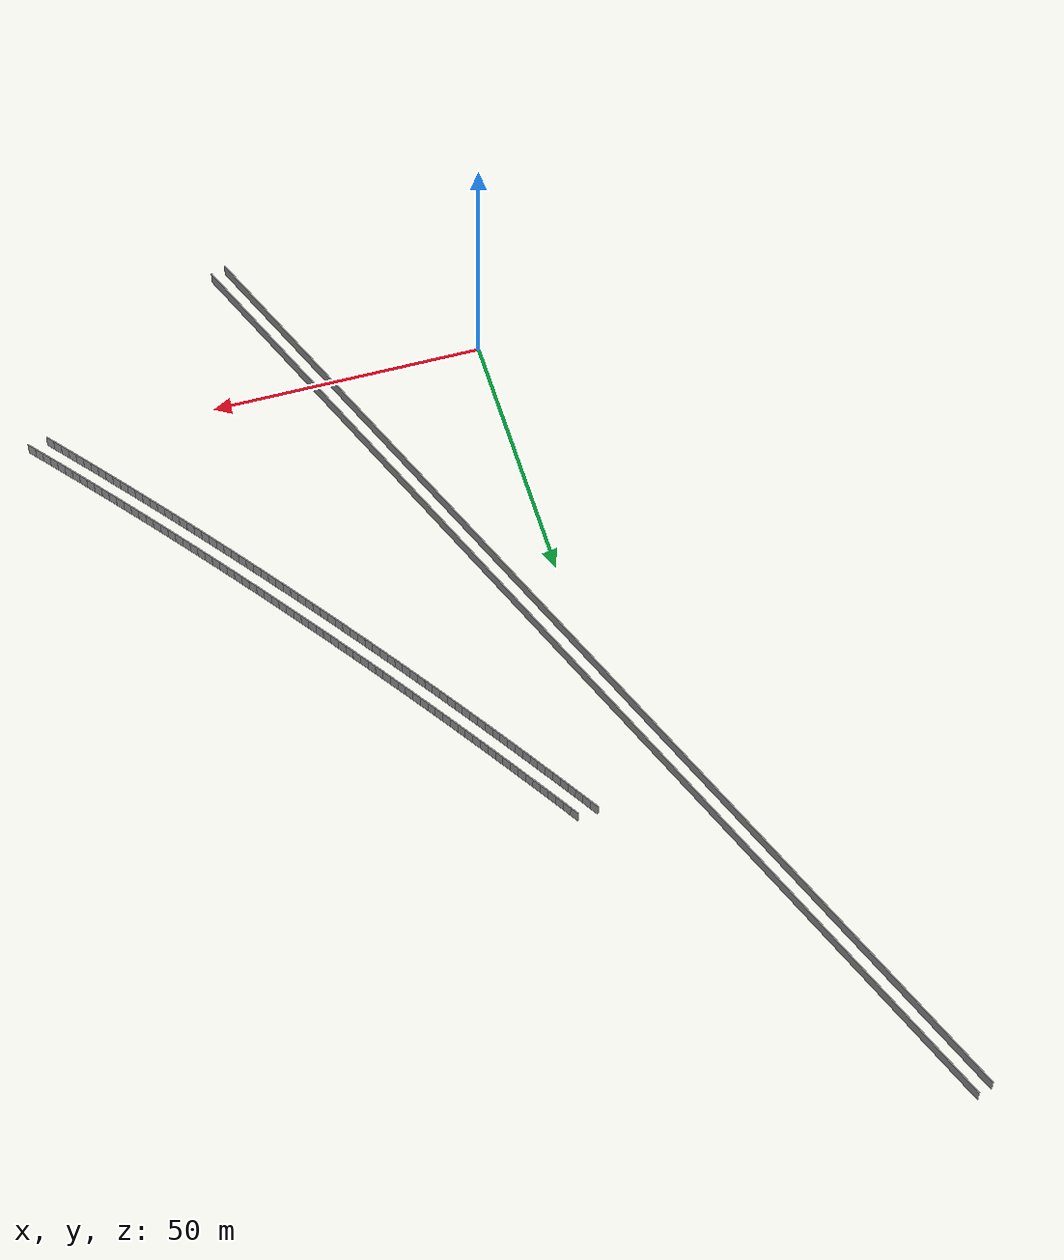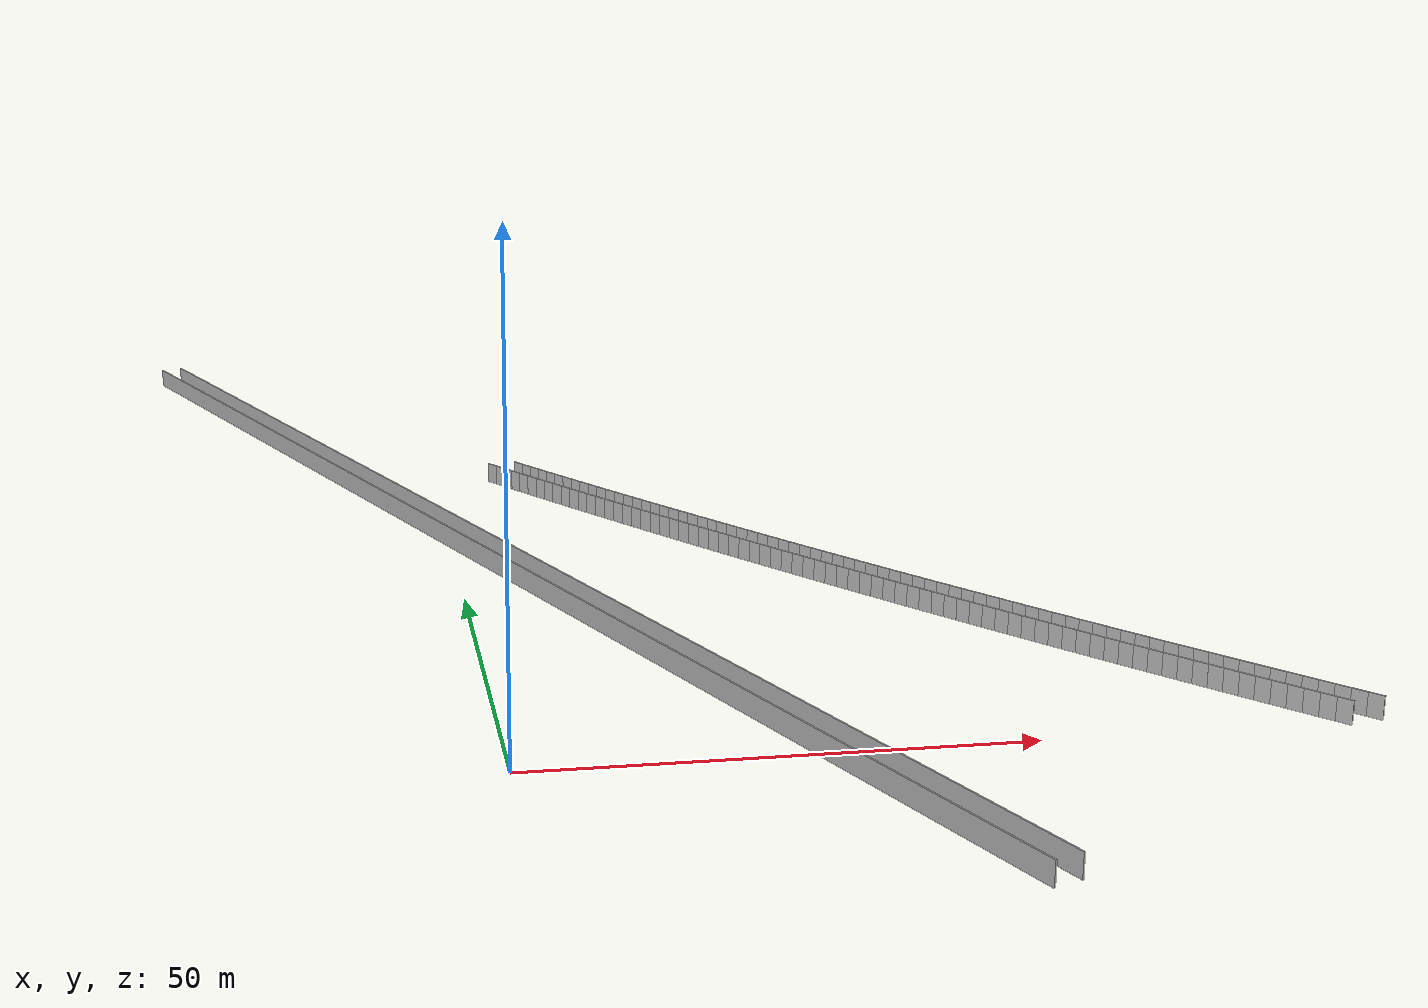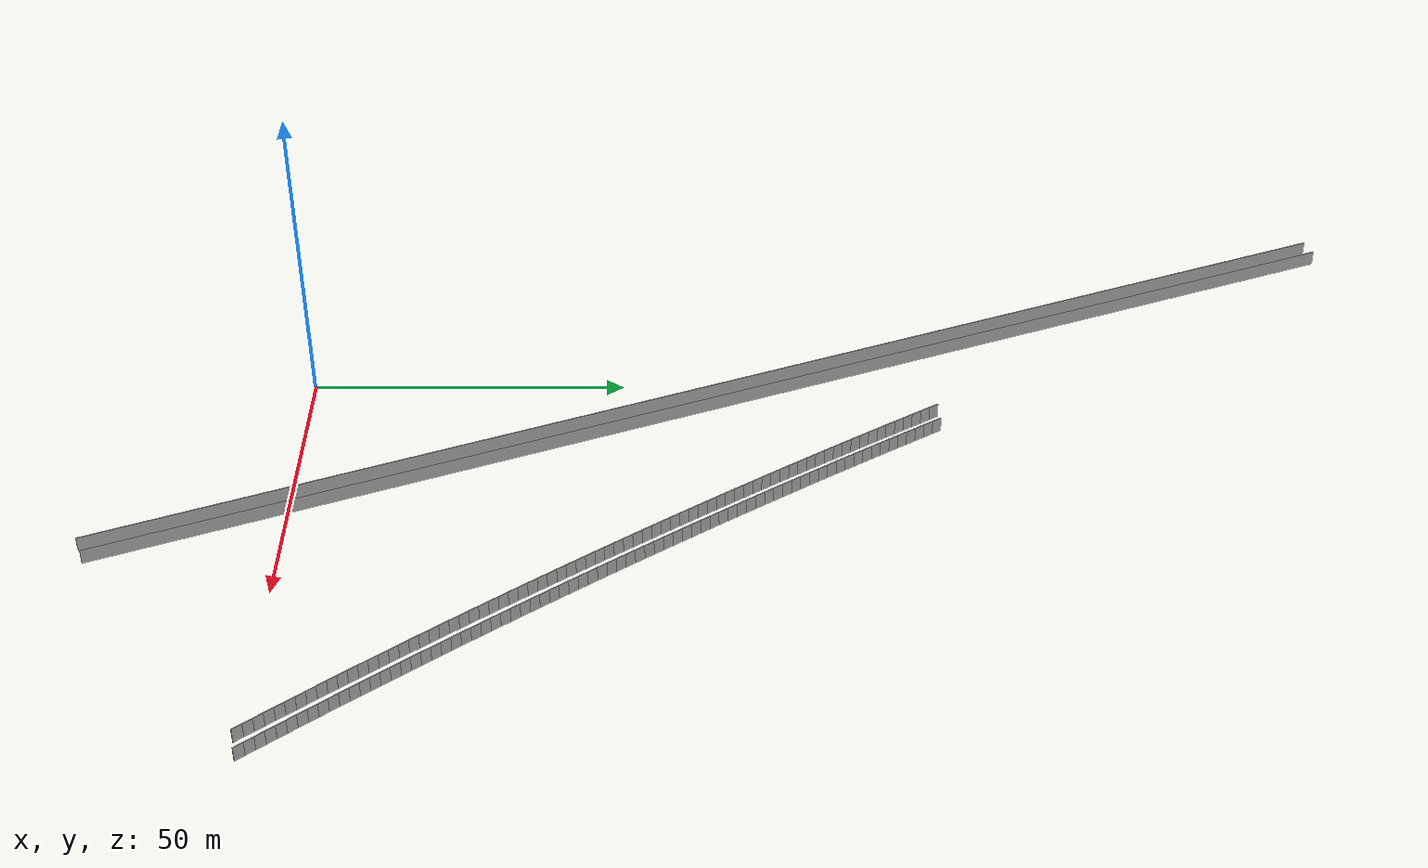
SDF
<?xml version="1.0" ?>
<sdf version="1.6">
  <model name="sps_2412">
    <pose frame="">0 0 0 0 -0 0</pose>
    <static>1</static>
    <self_collide>0</self_collide>
    <allow_auto_disable>0</allow_auto_disable>
    <link name="Wall3543">
      <kinematic>0</kinematic>
      <gravity>1</gravity>
      <self_collide>0</self_collide>
      <collision name="collision">
        <geometry>
          <box>
            <size>212.029 0.15 2.5</size>
          </box>
        </geometry>
        <pose frame="">0 0 0 0 -0 0</pose>
      </collision>
      <visual name="visual">
        <geometry>
          <box>
            <size>212.029 0.15 2.5</size>
          </box>
        </geometry>
        <pose frame="">0 0 0 0 -0 0</pose>
        <cast_shadows>1</cast_shadows>
        <transparency>0.0</transparency>
      </visual>
      <pose frame="">0.909141 68.134 1.25 0 0 -1.18648</pose>
    </link>
    <link name="Wall6538">
      <kinematic>0</kinematic>
      <gravity>1</gravity>
      <self_collide>0</self_collide>
      <collision name="collision">
        <geometry>
          <box>
            <size>1.68629 0.15 2.5</size>
          </box>
        </geometry>
        <pose frame="">0 0 0 0 -0 0</pose>
      </collision>
      <visual name="visual">
        <geometry>
          <box>
            <size>1.68629 0.15 2.5</size>
          </box>
        </geometry>
        <pose frame="">0 0 0 0 -0 0</pose>
        <cast_shadows>1</cast_shadows>
        <transparency>0.0</transparency>
      </visual>
      <pose frame="">7.78435 99.5371 1.25 0 0 -1.00286</pose>
    </link>
    <link name="Wall6539">
      <kinematic>0</kinematic>
      <gravity>1</gravity>
      <self_collide>0</self_collide>
      <collision name="collision">
        <geometry>
          <box>
            <size>1.68605 0.15 2.5</size>
          </box>
        </geometry>
        <pose frame="">0 0 0 0 -0 0</pose>
      </collision>
      <visual name="visual">
        <geometry>
          <box>
            <size>1.68605 0.15 2.5</size>
          </box>
        </geometry>
        <pose frame="">0 0 0 0 -0 0</pose>
        <cast_shadows>1</cast_shadows>
        <transparency>0.0</transparency>
      </visual>
      <pose frame="">8.69256 98.1164 1.25 0 0 -1.00114</pose>
    </link>
    <link name="Wall6540">
      <kinematic>0</kinematic>
      <gravity>1</gravity>
      <self_collide>0</self_collide>
      <collision name="collision">
        <geometry>
          <box>
            <size>1.68639 0.15 2.5</size>
          </box>
        </geometry>
        <pose frame="">0 0 0 0 -0 0</pose>
      </collision>
      <visual name="visual">
        <geometry>
          <box>
            <size>1.68639 0.15 2.5</size>
          </box>
        </geometry>
        <pose frame="">0 0 0 0 -0 0</pose>
        <cast_shadows>1</cast_shadows>
        <transparency>0.0</transparency>
      </visual>
      <pose frame="">9.60314 96.6972 1.25 0 0 -0.999548</pose>
    </link>
    <link name="Wall6541">
      <kinematic>0</kinematic>
      <gravity>1</gravity>
      <self_collide>0</self_collide>
      <collision name="collision">
        <geometry>
          <box>
            <size>1.68609 0.15 2.5</size>
          </box>
        </geometry>
        <pose frame="">0 0 0 0 -0 0</pose>
      </collision>
      <visual name="visual">
        <geometry>
          <box>
            <size>1.68609 0.15 2.5</size>
          </box>
        </geometry>
        <pose frame="">0 0 0 0 -0 0</pose>
        <cast_shadows>1</cast_shadows>
        <transparency>0.0</transparency>
      </visual>
      <pose frame="">10.5161 95.2795 1.25 0 0 -0.997754</pose>
    </link>
    <link name="Wall6542">
      <kinematic>0</kinematic>
      <gravity>1</gravity>
      <self_collide>0</self_collide>
      <collision name="collision">
        <geometry>
          <box>
            <size>1.68629 0.15 2.5</size>
          </box>
        </geometry>
        <pose frame="">0 0 0 0 -0 0</pose>
      </collision>
      <visual name="visual">
        <geometry>
          <box>
            <size>1.68629 0.15 2.5</size>
          </box>
        </geometry>
        <pose frame="">0 0 0 0 -0 0</pose>
        <cast_shadows>1</cast_shadows>
        <transparency>0.0</transparency>
      </visual>
      <pose frame="">11.4315 93.8634 1.25 0 0 -0.996105</pose>
    </link>
    <link name="Wall6543">
      <kinematic>0</kinematic>
      <gravity>1</gravity>
      <self_collide>0</self_collide>
      <collision name="collision">
        <geometry>
          <box>
            <size>1.686 0.15 2.5</size>
          </box>
        </geometry>
        <pose frame="">0 0 0 0 -0 0</pose>
      </collision>
      <visual name="visual">
        <geometry>
          <box>
            <size>1.686 0.15 2.5</size>
          </box>
        </geometry>
        <pose frame="">0 0 0 0 -0 0</pose>
        <cast_shadows>1</cast_shadows>
        <transparency>0.0</transparency>
      </visual>
      <pose frame="">12.3493 92.4489 1.25 0 0 -0.994441</pose>
    </link>
    <link name="Wall6544">
      <kinematic>0</kinematic>
      <gravity>1</gravity>
      <self_collide>0</self_collide>
      <collision name="collision">
        <geometry>
          <box>
            <size>1.68638 0.15 2.5</size>
          </box>
        </geometry>
        <pose frame="">0 0 0 0 -0 0</pose>
      </collision>
      <visual name="visual">
        <geometry>
          <box>
            <size>1.68638 0.15 2.5</size>
          </box>
        </geometry>
        <pose frame="">0 0 0 0 -0 0</pose>
        <cast_shadows>1</cast_shadows>
        <transparency>0.0</transparency>
      </visual>
      <pose frame="">13.2694 91.0359 1.25 0 0 -0.992772</pose>
    </link>
    <link name="Wall6545">
      <kinematic>0</kinematic>
      <gravity>1</gravity>
      <self_collide>0</self_collide>
      <collision name="collision">
        <geometry>
          <box>
            <size>1.68605 0.15 2.5</size>
          </box>
        </geometry>
        <pose frame="">0 0 0 0 -0 0</pose>
      </collision>
      <visual name="visual">
        <geometry>
          <box>
            <size>1.68605 0.15 2.5</size>
          </box>
        </geometry>
        <pose frame="">0 0 0 0 -0 0</pose>
        <cast_shadows>1</cast_shadows>
        <transparency>0.0</transparency>
      </visual>
      <pose frame="">14.1919 89.6244 1.25 0 0 -0.991087</pose>
    </link>
    <link name="Wall6546">
      <kinematic>0</kinematic>
      <gravity>1</gravity>
      <self_collide>0</self_collide>
      <collision name="collision">
        <geometry>
          <box>
            <size>1.68631 0.15 2.5</size>
          </box>
        </geometry>
        <pose frame="">0 0 0 0 -0 0</pose>
      </collision>
      <visual name="visual">
        <geometry>
          <box>
            <size>1.68631 0.15 2.5</size>
          </box>
        </geometry>
        <pose frame="">0 0 0 0 -0 0</pose>
        <cast_shadows>1</cast_shadows>
        <transparency>0.0</transparency>
      </visual>
      <pose frame="">15.1168 88.2145 1.25 0 0 -0.989329</pose>
    </link>
    <link name="Wall6547">
      <kinematic>0</kinematic>
      <gravity>1</gravity>
      <self_collide>0</self_collide>
      <collision name="collision">
        <geometry>
          <box>
            <size>1.68604 0.15 2.5</size>
          </box>
        </geometry>
        <pose frame="">0 0 0 0 -0 0</pose>
      </collision>
      <visual name="visual">
        <geometry>
          <box>
            <size>1.68604 0.15 2.5</size>
          </box>
        </geometry>
        <pose frame="">0 0 0 0 -0 0</pose>
        <cast_shadows>1</cast_shadows>
        <transparency>0.0</transparency>
      </visual>
      <pose frame="">16.0441 86.8062 1.25 0 0 -0.987663</pose>
    </link>
    <link name="Wall6548">
      <kinematic>0</kinematic>
      <gravity>1</gravity>
      <self_collide>0</self_collide>
      <collision name="collision">
        <geometry>
          <box>
            <size>1.68634 0.15 2.5</size>
          </box>
        </geometry>
        <pose frame="">0 0 0 0 -0 0</pose>
      </collision>
      <visual name="visual">
        <geometry>
          <box>
            <size>1.68634 0.15 2.5</size>
          </box>
        </geometry>
        <pose frame="">0 0 0 0 -0 0</pose>
        <cast_shadows>1</cast_shadows>
        <transparency>0.0</transparency>
      </visual>
      <pose frame="">16.9737 85.3994 1.25 0 0 -0.986086</pose>
    </link>
    <link name="Wall6549">
      <kinematic>0</kinematic>
      <gravity>1</gravity>
      <self_collide>0</self_collide>
      <collision name="collision">
        <geometry>
          <box>
            <size>1.68608 0.15 2.5</size>
          </box>
        </geometry>
        <pose frame="">0 0 0 0 -0 0</pose>
      </collision>
      <visual name="visual">
        <geometry>
          <box>
            <size>1.68608 0.15 2.5</size>
          </box>
        </geometry>
        <pose frame="">0 0 0 0 -0 0</pose>
        <cast_shadows>1</cast_shadows>
        <transparency>0.0</transparency>
      </visual>
      <pose frame="">17.9055 83.9941 1.25 0 0 -0.98442</pose>
    </link>
    <link name="Wall6550">
      <kinematic>0</kinematic>
      <gravity>1</gravity>
      <self_collide>0</self_collide>
      <collision name="collision">
        <geometry>
          <box>
            <size>1.68636 0.15 2.5</size>
          </box>
        </geometry>
        <pose frame="">0 0 0 0 -0 0</pose>
      </collision>
      <visual name="visual">
        <geometry>
          <box>
            <size>1.68636 0.15 2.5</size>
          </box>
        </geometry>
        <pose frame="">0 0 0 0 -0 0</pose>
        <cast_shadows>1</cast_shadows>
        <transparency>0.0</transparency>
      </visual>
      <pose frame="">18.8398 82.5904 1.25 0 0 -0.982663</pose>
    </link>
    <link name="Wall6551">
      <kinematic>0</kinematic>
      <gravity>1</gravity>
      <self_collide>0</self_collide>
      <collision name="collision">
        <geometry>
          <box>
            <size>1.68604 0.15 2.5</size>
          </box>
        </geometry>
        <pose frame="">0 0 0 0 -0 0</pose>
      </collision>
      <visual name="visual">
        <geometry>
          <box>
            <size>1.68604 0.15 2.5</size>
          </box>
        </geometry>
        <pose frame="">0 0 0 0 -0 0</pose>
        <cast_shadows>1</cast_shadows>
        <transparency>0.0</transparency>
      </visual>
      <pose frame="">19.7768 81.1885 1.25 0 0 -0.980535</pose>
    </link>
    <link name="Wall6552">
      <kinematic>0</kinematic>
      <gravity>1</gravity>
      <self_collide>0</self_collide>
      <collision name="collision">
        <geometry>
          <box>
            <size>1.68641 0.15 2.5</size>
          </box>
        </geometry>
        <pose frame="">0 0 0 0 -0 0</pose>
      </collision>
      <visual name="visual">
        <geometry>
          <box>
            <size>1.68641 0.15 2.5</size>
          </box>
        </geometry>
        <pose frame="">0 0 0 0 -0 0</pose>
        <cast_shadows>1</cast_shadows>
        <transparency>0.0</transparency>
      </visual>
      <pose frame="">20.7163 79.7882 1.25 0 0 -0.97924</pose>
    </link>
    <link name="Wall6553">
      <kinematic>0</kinematic>
      <gravity>1</gravity>
      <self_collide>0</self_collide>
      <collision name="collision">
        <geometry>
          <box>
            <size>1.68598 0.15 2.5</size>
          </box>
        </geometry>
        <pose frame="">0 0 0 0 -0 0</pose>
      </collision>
      <visual name="visual">
        <geometry>
          <box>
            <size>1.68598 0.15 2.5</size>
          </box>
        </geometry>
        <pose frame="">0 0 0 0 -0 0</pose>
        <cast_shadows>1</cast_shadows>
        <transparency>0.0</transparency>
      </visual>
      <pose frame="">21.6579 78.3894 1.25 0 0 -0.977412</pose>
    </link>
    <link name="Wall6554">
      <kinematic>0</kinematic>
      <gravity>1</gravity>
      <self_collide>0</self_collide>
      <collision name="collision">
        <geometry>
          <box>
            <size>1.68628 0.15 2.5</size>
          </box>
        </geometry>
        <pose frame="">0 0 0 0 -0 0</pose>
      </collision>
      <visual name="visual">
        <geometry>
          <box>
            <size>1.68628 0.15 2.5</size>
          </box>
        </geometry>
        <pose frame="">0 0 0 0 -0 0</pose>
        <cast_shadows>1</cast_shadows>
        <transparency>0.0</transparency>
      </visual>
      <pose frame="">22.6017 76.9922 1.25 0 0 -0.975917</pose>
    </link>
    <link name="Wall6555">
      <kinematic>0</kinematic>
      <gravity>1</gravity>
      <self_collide>0</self_collide>
      <collision name="collision">
        <geometry>
          <box>
            <size>1.6861 0.15 2.5</size>
          </box>
        </geometry>
        <pose frame="">0 0 0 0 -0 0</pose>
      </collision>
      <visual name="visual">
        <geometry>
          <box>
            <size>1.6861 0.15 2.5</size>
          </box>
        </geometry>
        <pose frame="">0 0 0 0 -0 0</pose>
        <cast_shadows>1</cast_shadows>
        <transparency>0.0</transparency>
      </visual>
      <pose frame="">23.5479 75.5965 1.25 0 0 -0.974139</pose>
    </link>
    <link name="Wall6556">
      <kinematic>0</kinematic>
      <gravity>1</gravity>
      <self_collide>0</self_collide>
      <collision name="collision">
        <geometry>
          <box>
            <size>1.68611 0.15 2.5</size>
          </box>
        </geometry>
        <pose frame="">0 0 0 0 -0 0</pose>
      </collision>
      <visual name="visual">
        <geometry>
          <box>
            <size>1.68611 0.15 2.5</size>
          </box>
        </geometry>
        <pose frame="">0 0 0 0 -0 0</pose>
        <cast_shadows>1</cast_shadows>
        <transparency>0.0</transparency>
      </visual>
      <pose frame="">24.4965 74.2025 1.25 0 0 -0.972523</pose>
    </link>
    <link name="Wall6557">
      <kinematic>0</kinematic>
      <gravity>1</gravity>
      <self_collide>0</self_collide>
      <collision name="collision">
        <geometry>
          <box>
            <size>1.68621 0.15 2.5</size>
          </box>
        </geometry>
        <pose frame="">0 0 0 0 -0 0</pose>
      </collision>
      <visual name="visual">
        <geometry>
          <box>
            <size>1.68621 0.15 2.5</size>
          </box>
        </geometry>
        <pose frame="">0 0 0 0 -0 0</pose>
        <cast_shadows>1</cast_shadows>
        <transparency>0.0</transparency>
      </visual>
      <pose frame="">25.4473 72.81 1.25 0 0 -0.970897</pose>
    </link>
    <link name="Wall6558">
      <kinematic>0</kinematic>
      <gravity>1</gravity>
      <self_collide>0</self_collide>
      <collision name="collision">
        <geometry>
          <box>
            <size>1.68628 0.15 2.5</size>
          </box>
        </geometry>
        <pose frame="">0 0 0 0 -0 0</pose>
      </collision>
      <visual name="visual">
        <geometry>
          <box>
            <size>1.68628 0.15 2.5</size>
          </box>
        </geometry>
        <pose frame="">0 0 0 0 -0 0</pose>
        <cast_shadows>1</cast_shadows>
        <transparency>0.0</transparency>
      </visual>
      <pose frame="">26.4004 71.419 1.25 0 0 -0.969171</pose>
    </link>
    <link name="Wall6559">
      <kinematic>0</kinematic>
      <gravity>1</gravity>
      <self_collide>0</self_collide>
      <collision name="collision">
        <geometry>
          <box>
            <size>1.68632 0.15 2.5</size>
          </box>
        </geometry>
        <pose frame="">0 0 0 0 -0 0</pose>
      </collision>
      <visual name="visual">
        <geometry>
          <box>
            <size>1.68632 0.15 2.5</size>
          </box>
        </geometry>
        <pose frame="">0 0 0 0 -0 0</pose>
        <cast_shadows>1</cast_shadows>
        <transparency>0.0</transparency>
      </visual>
      <pose frame="">27.356 70.0296 1.25 0 0 -0.967474</pose>
    </link>
    <link name="Wall6560">
      <kinematic>0</kinematic>
      <gravity>1</gravity>
      <self_collide>0</self_collide>
      <collision name="collision">
        <geometry>
          <box>
            <size>1.6861 0.15 2.5</size>
          </box>
        </geometry>
        <pose frame="">0 0 0 0 -0 0</pose>
      </collision>
      <visual name="visual">
        <geometry>
          <box>
            <size>1.6861 0.15 2.5</size>
          </box>
        </geometry>
        <pose frame="">0 0 0 0 -0 0</pose>
        <cast_shadows>1</cast_shadows>
        <transparency>0.0</transparency>
      </visual>
      <pose frame="">28.314 68.6419 1.25 0 0 -0.965755</pose>
    </link>
    <link name="Wall6561">
      <kinematic>0</kinematic>
      <gravity>1</gravity>
      <self_collide>0</self_collide>
      <collision name="collision">
        <geometry>
          <box>
            <size>1.68631 0.15 2.5</size>
          </box>
        </geometry>
        <pose frame="">0 0 0 0 -0 0</pose>
      </collision>
      <visual name="visual">
        <geometry>
          <box>
            <size>1.68631 0.15 2.5</size>
          </box>
        </geometry>
        <pose frame="">0 0 0 0 -0 0</pose>
        <cast_shadows>1</cast_shadows>
        <transparency>0.0</transparency>
      </visual>
      <pose frame="">29.2742 67.2558 1.25 0 0 -0.964171</pose>
    </link>
    <link name="Wall6562">
      <kinematic>0</kinematic>
      <gravity>1</gravity>
      <self_collide>0</self_collide>
      <collision name="collision">
        <geometry>
          <box>
            <size>1.68616 0.15 2.5</size>
          </box>
        </geometry>
        <pose frame="">0 0 0 0 -0 0</pose>
      </collision>
      <visual name="visual">
        <geometry>
          <box>
            <size>1.68616 0.15 2.5</size>
          </box>
        </geometry>
        <pose frame="">0 0 0 0 -0 0</pose>
        <cast_shadows>1</cast_shadows>
        <transparency>0.0</transparency>
      </visual>
      <pose frame="">30.2367 65.8713 1.25 0 0 -0.962342</pose>
    </link>
    <link name="Wall6563">
      <kinematic>0</kinematic>
      <gravity>1</gravity>
      <self_collide>0</self_collide>
      <collision name="collision">
        <geometry>
          <box>
            <size>1.68616 0.15 2.5</size>
          </box>
        </geometry>
        <pose frame="">0 0 0 0 -0 0</pose>
      </collision>
      <visual name="visual">
        <geometry>
          <box>
            <size>1.68616 0.15 2.5</size>
          </box>
        </geometry>
        <pose frame="">0 0 0 0 -0 0</pose>
        <cast_shadows>1</cast_shadows>
        <transparency>0.0</transparency>
      </visual>
      <pose frame="">31.2017 64.4885 1.25 0 0 -0.960755</pose>
    </link>
    <link name="Wall6564">
      <kinematic>0</kinematic>
      <gravity>1</gravity>
      <self_collide>0</self_collide>
      <collision name="collision">
        <geometry>
          <box>
            <size>1.68623 0.15 2.5</size>
          </box>
        </geometry>
        <pose frame="">0 0 0 0 -0 0</pose>
      </collision>
      <visual name="visual">
        <geometry>
          <box>
            <size>1.68623 0.15 2.5</size>
          </box>
        </geometry>
        <pose frame="">0 0 0 0 -0 0</pose>
        <cast_shadows>1</cast_shadows>
        <transparency>0.0</transparency>
      </visual>
      <pose frame="">32.1688 63.1073 1.25 0 0 -0.959059</pose>
    </link>
    <link name="Wall6565">
      <kinematic>0</kinematic>
      <gravity>1</gravity>
      <self_collide>0</self_collide>
      <collision name="collision">
        <geometry>
          <box>
            <size>1.68603 0.15 2.5</size>
          </box>
        </geometry>
        <pose frame="">0 0 0 0 -0 0</pose>
      </collision>
      <visual name="visual">
        <geometry>
          <box>
            <size>1.68603 0.15 2.5</size>
          </box>
        </geometry>
        <pose frame="">0 0 0 0 -0 0</pose>
        <cast_shadows>1</cast_shadows>
        <transparency>0.0</transparency>
      </visual>
      <pose frame="">33.1384 61.7278 1.25 0 0 -0.957339</pose>
    </link>
    <link name="Wall6566">
      <kinematic>0</kinematic>
      <gravity>1</gravity>
      <self_collide>0</self_collide>
      <collision name="collision">
        <geometry>
          <box>
            <size>1.68622 0.15 2.5</size>
          </box>
        </geometry>
        <pose frame="">0 0 0 0 -0 0</pose>
      </collision>
      <visual name="visual">
        <geometry>
          <box>
            <size>1.68622 0.15 2.5</size>
          </box>
        </geometry>
        <pose frame="">0 0 0 0 -0 0</pose>
        <cast_shadows>1</cast_shadows>
        <transparency>0.0</transparency>
      </visual>
      <pose frame="">34.1102 60.3499 1.25 0 0 -0.955735</pose>
    </link>
    <link name="Wall6567">
      <kinematic>0</kinematic>
      <gravity>1</gravity>
      <self_collide>0</self_collide>
      <collision name="collision">
        <geometry>
          <box>
            <size>1.68628 0.15 2.5</size>
          </box>
        </geometry>
        <pose frame="">0 0 0 0 -0 0</pose>
      </collision>
      <visual name="visual">
        <geometry>
          <box>
            <size>1.68628 0.15 2.5</size>
          </box>
        </geometry>
        <pose frame="">0 0 0 0 -0 0</pose>
        <cast_shadows>1</cast_shadows>
        <transparency>0.0</transparency>
      </visual>
      <pose frame="">35.0843 58.9735 1.25 0 0 -0.953989</pose>
    </link>
    <link name="Wall6568">
      <kinematic>0</kinematic>
      <gravity>1</gravity>
      <self_collide>0</self_collide>
      <collision name="collision">
        <geometry>
          <box>
            <size>1.68616 0.15 2.5</size>
          </box>
        </geometry>
        <pose frame="">0 0 0 0 -0 0</pose>
      </collision>
      <visual name="visual">
        <geometry>
          <box>
            <size>1.68616 0.15 2.5</size>
          </box>
        </geometry>
        <pose frame="">0 0 0 0 -0 0</pose>
        <cast_shadows>1</cast_shadows>
        <transparency>0.0</transparency>
      </visual>
      <pose frame="">36.0608 57.5988 1.25 0 0 -0.952339</pose>
    </link>
    <link name="Wall6569">
      <kinematic>0</kinematic>
      <gravity>1</gravity>
      <self_collide>0</self_collide>
      <collision name="collision">
        <geometry>
          <box>
            <size>1.68624 0.15 2.5</size>
          </box>
        </geometry>
        <pose frame="">0 0 0 0 -0 0</pose>
      </collision>
      <visual name="visual">
        <geometry>
          <box>
            <size>1.68624 0.15 2.5</size>
          </box>
        </geometry>
        <pose frame="">0 0 0 0 -0 0</pose>
        <cast_shadows>1</cast_shadows>
        <transparency>0.0</transparency>
      </visual>
      <pose frame="">37.0397 56.2258 1.25 0 0 -0.950593</pose>
    </link>
    <link name="Wall6570">
      <kinematic>0</kinematic>
      <gravity>1</gravity>
      <self_collide>0</self_collide>
      <collision name="collision">
        <geometry>
          <box>
            <size>1.6863 0.15 2.5</size>
          </box>
        </geometry>
        <pose frame="">0 0 0 0 -0 0</pose>
      </collision>
      <visual name="visual">
        <geometry>
          <box>
            <size>1.6863 0.15 2.5</size>
          </box>
        </geometry>
        <pose frame="">0 0 0 0 -0 0</pose>
        <cast_shadows>1</cast_shadows>
        <transparency>0.0</transparency>
      </visual>
      <pose frame="">38.0209 54.8544 1.25 0 0 -0.948927</pose>
    </link>
    <link name="Wall6571">
      <kinematic>0</kinematic>
      <gravity>1</gravity>
      <self_collide>0</self_collide>
      <collision name="collision">
        <geometry>
          <box>
            <size>1.68632 0.15 2.5</size>
          </box>
        </geometry>
        <pose frame="">0 0 0 0 -0 0</pose>
      </collision>
      <visual name="visual">
        <geometry>
          <box>
            <size>1.68632 0.15 2.5</size>
          </box>
        </geometry>
        <pose frame="">0 0 0 0 -0 0</pose>
        <cast_shadows>1</cast_shadows>
        <transparency>0.0</transparency>
      </visual>
      <pose frame="">39.0044 53.4846 1.25 0 0 -0.94729</pose>
    </link>
    <link name="Wall6572">
      <kinematic>0</kinematic>
      <gravity>1</gravity>
      <self_collide>0</self_collide>
      <collision name="collision">
        <geometry>
          <box>
            <size>1.68612 0.15 2.5</size>
          </box>
        </geometry>
        <pose frame="">0 0 0 0 -0 0</pose>
      </collision>
      <visual name="visual">
        <geometry>
          <box>
            <size>1.68612 0.15 2.5</size>
          </box>
        </geometry>
        <pose frame="">0 0 0 0 -0 0</pose>
        <cast_shadows>1</cast_shadows>
        <transparency>0.0</transparency>
      </visual>
      <pose frame="">39.9901 52.1165 1.25 0 0 -0.945598</pose>
    </link>
    <link name="Wall6573">
      <kinematic>0</kinematic>
      <gravity>1</gravity>
      <self_collide>0</self_collide>
      <collision name="collision">
        <geometry>
          <box>
            <size>1.68603 0.15 2.5</size>
          </box>
        </geometry>
        <pose frame="">0 0 0 0 -0 0</pose>
      </collision>
      <visual name="visual">
        <geometry>
          <box>
            <size>1.68603 0.15 2.5</size>
          </box>
        </geometry>
        <pose frame="">0 0 0 0 -0 0</pose>
        <cast_shadows>1</cast_shadows>
        <transparency>0.0</transparency>
      </visual>
      <pose frame="">40.9781 50.7502 1.25 0 0 -0.943818</pose>
    </link>
    <link name="Wall6574">
      <kinematic>0</kinematic>
      <gravity>1</gravity>
      <self_collide>0</self_collide>
      <collision name="collision">
        <geometry>
          <box>
            <size>1.6862 0.15 2.5</size>
          </box>
        </geometry>
        <pose frame="">0 0 0 0 -0 0</pose>
      </collision>
      <visual name="visual">
        <geometry>
          <box>
            <size>1.6862 0.15 2.5</size>
          </box>
        </geometry>
        <pose frame="">0 0 0 0 -0 0</pose>
        <cast_shadows>1</cast_shadows>
        <transparency>0.0</transparency>
      </visual>
      <pose frame="">41.9685 49.3856 1.25 0 0 -0.942144</pose>
    </link>
    <link name="Wall6575">
      <kinematic>0</kinematic>
      <gravity>1</gravity>
      <self_collide>0</self_collide>
      <collision name="collision">
        <geometry>
          <box>
            <size>1.68611 0.15 2.5</size>
          </box>
        </geometry>
        <pose frame="">0 0 0 0 -0 0</pose>
      </collision>
      <visual name="visual">
        <geometry>
          <box>
            <size>1.68611 0.15 2.5</size>
          </box>
        </geometry>
        <pose frame="">0 0 0 0 -0 0</pose>
        <cast_shadows>1</cast_shadows>
        <transparency>0.0</transparency>
      </visual>
      <pose frame="">42.9614 48.0228 1.25 0 0 -0.940182</pose>
    </link>
    <link name="Wall6576">
      <kinematic>0</kinematic>
      <gravity>1</gravity>
      <self_collide>0</self_collide>
      <collision name="collision">
        <geometry>
          <box>
            <size>1.68617 0.15 2.5</size>
          </box>
        </geometry>
        <pose frame="">0 0 0 0 -0 0</pose>
      </collision>
      <visual name="visual">
        <geometry>
          <box>
            <size>1.68617 0.15 2.5</size>
          </box>
        </geometry>
        <pose frame="">0 0 0 0 -0 0</pose>
        <cast_shadows>1</cast_shadows>
        <transparency>0.0</transparency>
      </visual>
      <pose frame="">43.9564 46.6616 1.25 0 0 -0.938908</pose>
    </link>
    <link name="Wall6577">
      <kinematic>0</kinematic>
      <gravity>1</gravity>
      <self_collide>0</self_collide>
      <collision name="collision">
        <geometry>
          <box>
            <size>1.68614 0.15 2.5</size>
          </box>
        </geometry>
        <pose frame="">0 0 0 0 -0 0</pose>
      </collision>
      <visual name="visual">
        <geometry>
          <box>
            <size>1.68614 0.15 2.5</size>
          </box>
        </geometry>
        <pose frame="">0 0 0 0 -0 0</pose>
        <cast_shadows>1</cast_shadows>
        <transparency>0.0</transparency>
      </visual>
      <pose frame="">44.9536 45.3019 1.25 0 0 -0.937098</pose>
    </link>
    <link name="Wall6578">
      <kinematic>0</kinematic>
      <gravity>1</gravity>
      <self_collide>0</self_collide>
      <collision name="collision">
        <geometry>
          <box>
            <size>1.68632 0.15 2.5</size>
          </box>
        </geometry>
        <pose frame="">0 0 0 0 -0 0</pose>
      </collision>
      <visual name="visual">
        <geometry>
          <box>
            <size>1.68632 0.15 2.5</size>
          </box>
        </geometry>
        <pose frame="">0 0 0 0 -0 0</pose>
        <cast_shadows>1</cast_shadows>
        <transparency>0.0</transparency>
      </visual>
      <pose frame="">45.9532 43.9439 1.25 0 0 -0.935425</pose>
    </link>
    <link name="Wall6579">
      <kinematic>0</kinematic>
      <gravity>1</gravity>
      <self_collide>0</self_collide>
      <collision name="collision">
        <geometry>
          <box>
            <size>1.68616 0.15 2.5</size>
          </box>
        </geometry>
        <pose frame="">0 0 0 0 -0 0</pose>
      </collision>
      <visual name="visual">
        <geometry>
          <box>
            <size>1.68616 0.15 2.5</size>
          </box>
        </geometry>
        <pose frame="">0 0 0 0 -0 0</pose>
        <cast_shadows>1</cast_shadows>
        <transparency>0.0</transparency>
      </visual>
      <pose frame="">46.9551 42.5876 1.25 0 0 -0.933731</pose>
    </link>
    <link name="Wall6580">
      <kinematic>0</kinematic>
      <gravity>1</gravity>
      <self_collide>0</self_collide>
      <collision name="collision">
        <geometry>
          <box>
            <size>1.68618 0.15 2.5</size>
          </box>
        </geometry>
        <pose frame="">0 0 0 0 -0 0</pose>
      </collision>
      <visual name="visual">
        <geometry>
          <box>
            <size>1.68618 0.15 2.5</size>
          </box>
        </geometry>
        <pose frame="">0 0 0 0 -0 0</pose>
        <cast_shadows>1</cast_shadows>
        <transparency>0.0</transparency>
      </visual>
      <pose frame="">47.9593 41.233 1.25 0 0 -0.932073</pose>
    </link>
    <link name="Wall6581">
      <kinematic>0</kinematic>
      <gravity>1</gravity>
      <self_collide>0</self_collide>
      <collision name="collision">
        <geometry>
          <box>
            <size>1.68634 0.15 2.5</size>
          </box>
        </geometry>
        <pose frame="">0 0 0 0 -0 0</pose>
      </collision>
      <visual name="visual">
        <geometry>
          <box>
            <size>1.68634 0.15 2.5</size>
          </box>
        </geometry>
        <pose frame="">0 0 0 0 -0 0</pose>
        <cast_shadows>1</cast_shadows>
        <transparency>0.0</transparency>
      </visual>
      <pose frame="">48.9657 39.88 1.25 0 0 -0.93043</pose>
    </link>
    <link name="Wall6582">
      <kinematic>0</kinematic>
      <gravity>1</gravity>
      <self_collide>0</self_collide>
      <collision name="collision">
        <geometry>
          <box>
            <size>1.68622 0.15 2.5</size>
          </box>
        </geometry>
        <pose frame="">0 0 0 0 -0 0</pose>
      </collision>
      <visual name="visual">
        <geometry>
          <box>
            <size>1.68622 0.15 2.5</size>
          </box>
        </geometry>
        <pose frame="">0 0 0 0 -0 0</pose>
        <cast_shadows>1</cast_shadows>
        <transparency>0.0</transparency>
      </visual>
      <pose frame="">49.9744 38.5287 1.25 0 0 -0.928707</pose>
    </link>
    <link name="Wall6583">
      <kinematic>0</kinematic>
      <gravity>1</gravity>
      <self_collide>0</self_collide>
      <collision name="collision">
        <geometry>
          <box>
            <size>1.68618 0.15 2.5</size>
          </box>
        </geometry>
        <pose frame="">0 0 0 0 -0 0</pose>
      </collision>
      <visual name="visual">
        <geometry>
          <box>
            <size>1.68618 0.15 2.5</size>
          </box>
        </geometry>
        <pose frame="">0 0 0 0 -0 0</pose>
        <cast_shadows>1</cast_shadows>
        <transparency>0.0</transparency>
      </visual>
      <pose frame="">50.9854 37.1792 1.25 0 0 -0.926926</pose>
    </link>
    <link name="Wall6584">
      <kinematic>0</kinematic>
      <gravity>1</gravity>
      <self_collide>0</self_collide>
      <collision name="collision">
        <geometry>
          <box>
            <size>1.68609 0.15 2.5</size>
          </box>
        </geometry>
        <pose frame="">0 0 0 0 -0 0</pose>
      </collision>
      <visual name="visual">
        <geometry>
          <box>
            <size>1.68609 0.15 2.5</size>
          </box>
        </geometry>
        <pose frame="">0 0 0 0 -0 0</pose>
        <cast_shadows>1</cast_shadows>
        <transparency>0.0</transparency>
      </visual>
      <pose frame="">51.9986 35.8314 1.25 0 0 -0.925435</pose>
    </link>
    <link name="Wall6585">
      <kinematic>0</kinematic>
      <gravity>1</gravity>
      <self_collide>0</self_collide>
      <collision name="collision">
        <geometry>
          <box>
            <size>1.68644 0.15 2.5</size>
          </box>
        </geometry>
        <pose frame="">0 0 0 0 -0 0</pose>
      </collision>
      <visual name="visual">
        <geometry>
          <box>
            <size>1.68644 0.15 2.5</size>
          </box>
        </geometry>
        <pose frame="">0 0 0 0 -0 0</pose>
        <cast_shadows>1</cast_shadows>
        <transparency>0.0</transparency>
      </visual>
      <pose frame="">53.0141 34.4852 1.25 0 0 -0.923596</pose>
    </link>
    <link name="Wall6586">
      <kinematic>0</kinematic>
      <gravity>1</gravity>
      <self_collide>0</self_collide>
      <collision name="collision">
        <geometry>
          <box>
            <size>1.68606 0.15 2.5</size>
          </box>
        </geometry>
        <pose frame="">0 0 0 0 -0 0</pose>
      </collision>
      <visual name="visual">
        <geometry>
          <box>
            <size>1.68606 0.15 2.5</size>
          </box>
        </geometry>
        <pose frame="">0 0 0 0 -0 0</pose>
        <cast_shadows>1</cast_shadows>
        <transparency>0.0</transparency>
      </visual>
      <pose frame="">54.0319 33.1408 1.25 0 0 -0.921974</pose>
    </link>
    <link name="Wall6587">
      <kinematic>0</kinematic>
      <gravity>1</gravity>
      <self_collide>0</self_collide>
      <collision name="collision">
        <geometry>
          <box>
            <size>1.68619 0.15 2.5</size>
          </box>
        </geometry>
        <pose frame="">0 0 0 0 -0 0</pose>
      </collision>
      <visual name="visual">
        <geometry>
          <box>
            <size>1.68619 0.15 2.5</size>
          </box>
        </geometry>
        <pose frame="">0 0 0 0 -0 0</pose>
        <cast_shadows>1</cast_shadows>
        <transparency>0.0</transparency>
      </visual>
      <pose frame="">55.0519 31.7982 1.25 0 0 -0.920258</pose>
    </link>
    <link name="Wall6588">
      <kinematic>0</kinematic>
      <gravity>1</gravity>
      <self_collide>0</self_collide>
      <collision name="collision">
        <geometry>
          <box>
            <size>1.68626 0.15 2.5</size>
          </box>
        </geometry>
        <pose frame="">0 0 0 0 -0 0</pose>
      </collision>
      <visual name="visual">
        <geometry>
          <box>
            <size>1.68626 0.15 2.5</size>
          </box>
        </geometry>
        <pose frame="">0 0 0 0 -0 0</pose>
        <cast_shadows>1</cast_shadows>
        <transparency>0.0</transparency>
      </visual>
      <pose frame="">56.0741 30.4572 1.25 0 0 -0.918652</pose>
    </link>
    <link name="Wall6589">
      <kinematic>0</kinematic>
      <gravity>1</gravity>
      <self_collide>0</self_collide>
      <collision name="collision">
        <geometry>
          <box>
            <size>1.68603 0.15 2.5</size>
          </box>
        </geometry>
        <pose frame="">0 0 0 0 -0 0</pose>
      </collision>
      <visual name="visual">
        <geometry>
          <box>
            <size>1.68603 0.15 2.5</size>
          </box>
        </geometry>
        <pose frame="">0 0 0 0 -0 0</pose>
        <cast_shadows>1</cast_shadows>
        <transparency>0.0</transparency>
      </visual>
      <pose frame="">57.0987 29.118 1.25 0 0 -0.916862</pose>
    </link>
    <link name="Wall6590">
      <kinematic>0</kinematic>
      <gravity>1</gravity>
      <self_collide>0</self_collide>
      <collision name="collision">
        <geometry>
          <box>
            <size>1.68633 0.15 2.5</size>
          </box>
        </geometry>
        <pose frame="">0 0 0 0 -0 0</pose>
      </collision>
      <visual name="visual">
        <geometry>
          <box>
            <size>1.68633 0.15 2.5</size>
          </box>
        </geometry>
        <pose frame="">0 0 0 0 -0 0</pose>
        <cast_shadows>1</cast_shadows>
        <transparency>0.0</transparency>
      </visual>
      <pose frame="">58.1254 27.7805 1.25 0 0 -0.915264</pose>
    </link>
    <link name="Wall6591">
      <kinematic>0</kinematic>
      <gravity>1</gravity>
      <self_collide>0</self_collide>
      <collision name="collision">
        <geometry>
          <box>
            <size>1.68611 0.15 2.5</size>
          </box>
        </geometry>
        <pose frame="">0 0 0 0 -0 0</pose>
      </collision>
      <visual name="visual">
        <geometry>
          <box>
            <size>1.68611 0.15 2.5</size>
          </box>
        </geometry>
        <pose frame="">0 0 0 0 -0 0</pose>
        <cast_shadows>1</cast_shadows>
        <transparency>0.0</transparency>
      </visual>
      <pose frame="">59.1545 26.4447 1.25 0 0 -0.913474</pose>
    </link>
    <link name="Wall6592">
      <kinematic>0</kinematic>
      <gravity>1</gravity>
      <self_collide>0</self_collide>
      <collision name="collision">
        <geometry>
          <box>
            <size>1.6862 0.15 2.5</size>
          </box>
        </geometry>
        <pose frame="">0 0 0 0 -0 0</pose>
      </collision>
      <visual name="visual">
        <geometry>
          <box>
            <size>1.6862 0.15 2.5</size>
          </box>
        </geometry>
        <pose frame="">0 0 0 0 -0 0</pose>
        <cast_shadows>1</cast_shadows>
        <transparency>0.0</transparency>
      </visual>
      <pose frame="">60.1858 25.1107 1.25 0 0 -0.911867</pose>
    </link>
    <link name="Wall6593">
      <kinematic>0</kinematic>
      <gravity>1</gravity>
      <self_collide>0</self_collide>
      <collision name="collision">
        <geometry>
          <box>
            <size>1.68615 0.15 2.5</size>
          </box>
        </geometry>
        <pose frame="">0 0 0 0 -0 0</pose>
      </collision>
      <visual name="visual">
        <geometry>
          <box>
            <size>1.68615 0.15 2.5</size>
          </box>
        </geometry>
        <pose frame="">0 0 0 0 -0 0</pose>
        <cast_shadows>1</cast_shadows>
        <transparency>0.0</transparency>
      </visual>
      <pose frame="">61.2194 23.7784 1.25 0 0 -0.910194</pose>
    </link>
    <link name="Wall6594">
      <kinematic>0</kinematic>
      <gravity>1</gravity>
      <self_collide>0</self_collide>
      <collision name="collision">
        <geometry>
          <box>
            <size>1.68631 0.15 2.5</size>
          </box>
        </geometry>
        <pose frame="">0 0 0 0 -0 0</pose>
      </collision>
      <visual name="visual">
        <geometry>
          <box>
            <size>1.68631 0.15 2.5</size>
          </box>
        </geometry>
        <pose frame="">0 0 0 0 -0 0</pose>
        <cast_shadows>1</cast_shadows>
        <transparency>0.0</transparency>
      </visual>
      <pose frame="">62.2551 22.4478 1.25 0 0 -0.90848</pose>
    </link>
    <link name="Wall6595">
      <kinematic>0</kinematic>
      <gravity>1</gravity>
      <self_collide>0</self_collide>
      <collision name="collision">
        <geometry>
          <box>
            <size>1.68612 0.15 2.5</size>
          </box>
        </geometry>
        <pose frame="">0 0 0 0 -0 0</pose>
      </collision>
      <visual name="visual">
        <geometry>
          <box>
            <size>1.68612 0.15 2.5</size>
          </box>
        </geometry>
        <pose frame="">0 0 0 0 -0 0</pose>
        <cast_shadows>1</cast_shadows>
        <transparency>0.0</transparency>
      </visual>
      <pose frame="">63.2932 21.119 1.25 0 0 -0.90674</pose>
    </link>
    <link name="Wall6596">
      <kinematic>0</kinematic>
      <gravity>1</gravity>
      <self_collide>0</self_collide>
      <collision name="collision">
        <geometry>
          <box>
            <size>1.68622 0.15 2.5</size>
          </box>
        </geometry>
        <pose frame="">0 0 0 0 -0 0</pose>
      </collision>
      <visual name="visual">
        <geometry>
          <box>
            <size>1.68622 0.15 2.5</size>
          </box>
        </geometry>
        <pose frame="">0 0 0 0 -0 0</pose>
        <cast_shadows>1</cast_shadows>
        <transparency>0.0</transparency>
      </visual>
      <pose frame="">64.3335 19.792 1.25 0 0 -0.905083</pose>
    </link>
    <link name="Wall6597">
      <kinematic>0</kinematic>
      <gravity>1</gravity>
      <self_collide>0</self_collide>
      <collision name="collision">
        <geometry>
          <box>
            <size>1.68634 0.15 2.5</size>
          </box>
        </geometry>
        <pose frame="">0 0 0 0 -0 0</pose>
      </collision>
      <visual name="visual">
        <geometry>
          <box>
            <size>1.68634 0.15 2.5</size>
          </box>
        </geometry>
        <pose frame="">0 0 0 0 -0 0</pose>
        <cast_shadows>1</cast_shadows>
        <transparency>0.0</transparency>
      </visual>
      <pose frame="">65.3761 18.4666 1.25 0 0 -0.903528</pose>
    </link>
    <link name="Wall6598">
      <kinematic>0</kinematic>
      <gravity>1</gravity>
      <self_collide>0</self_collide>
      <collision name="collision">
        <geometry>
          <box>
            <size>1.68622 0.15 2.5</size>
          </box>
        </geometry>
        <pose frame="">0 0 0 0 -0 0</pose>
      </collision>
      <visual name="visual">
        <geometry>
          <box>
            <size>1.68622 0.15 2.5</size>
          </box>
        </geometry>
        <pose frame="">0 0 0 0 -0 0</pose>
        <cast_shadows>1</cast_shadows>
        <transparency>0.0</transparency>
      </visual>
      <pose frame="">66.4209 17.143 1.25 0 0 -0.901629</pose>
    </link>
    <link name="Wall6599">
      <kinematic>0</kinematic>
      <gravity>1</gravity>
      <self_collide>0</self_collide>
      <collision name="collision">
        <geometry>
          <box>
            <size>1.68605 0.15 2.5</size>
          </box>
        </geometry>
        <pose frame="">0 0 0 0 -0 0</pose>
      </collision>
      <visual name="visual">
        <geometry>
          <box>
            <size>1.68605 0.15 2.5</size>
          </box>
        </geometry>
        <pose frame="">0 0 0 0 -0 0</pose>
        <cast_shadows>1</cast_shadows>
        <transparency>0.0</transparency>
      </visual>
      <pose frame="">67.4679 15.8213 1.25 0 0 -0.900069</pose>
    </link>
    <link name="Wall6600">
      <kinematic>0</kinematic>
      <gravity>1</gravity>
      <self_collide>0</self_collide>
      <collision name="collision">
        <geometry>
          <box>
            <size>1.68611 0.15 2.5</size>
          </box>
        </geometry>
        <pose frame="">0 0 0 0 -0 0</pose>
      </collision>
      <visual name="visual">
        <geometry>
          <box>
            <size>1.68611 0.15 2.5</size>
          </box>
        </geometry>
        <pose frame="">0 0 0 0 -0 0</pose>
        <cast_shadows>1</cast_shadows>
        <transparency>0.0</transparency>
      </visual>
      <pose frame="">68.5171 14.5015 1.25 0 0 -0.898108</pose>
    </link>
    <link name="Wall6601">
      <kinematic>0</kinematic>
      <gravity>1</gravity>
      <self_collide>0</self_collide>
      <collision name="collision">
        <geometry>
          <box>
            <size>1.6862 0.15 2.5</size>
          </box>
        </geometry>
        <pose frame="">0 0 0 0 -0 0</pose>
      </collision>
      <visual name="visual">
        <geometry>
          <box>
            <size>1.6862 0.15 2.5</size>
          </box>
        </geometry>
        <pose frame="">0 0 0 0 -0 0</pose>
        <cast_shadows>1</cast_shadows>
        <transparency>0.0</transparency>
      </visual>
      <pose frame="">69.5687 13.1834 1.25 0 0 -0.896762</pose>
    </link>
    <link name="Wall6602">
      <kinematic>0</kinematic>
      <gravity>1</gravity>
      <self_collide>0</self_collide>
      <collision name="collision">
        <geometry>
          <box>
            <size>1.68621 0.15 2.5</size>
          </box>
        </geometry>
        <pose frame="">0 0 0 0 -0 0</pose>
      </collision>
      <visual name="visual">
        <geometry>
          <box>
            <size>1.68621 0.15 2.5</size>
          </box>
        </geometry>
        <pose frame="">0 0 0 0 -0 0</pose>
        <cast_shadows>1</cast_shadows>
        <transparency>0.0</transparency>
      </visual>
      <pose frame="">70.6223 11.8669 1.25 0 0 -0.894959</pose>
    </link>
    <link name="Wall6603">
      <kinematic>0</kinematic>
      <gravity>1</gravity>
      <self_collide>0</self_collide>
      <collision name="collision">
        <geometry>
          <box>
            <size>1.68621 0.15 2.5</size>
          </box>
        </geometry>
        <pose frame="">0 0 0 0 -0 0</pose>
      </collision>
      <visual name="visual">
        <geometry>
          <box>
            <size>1.68621 0.15 2.5</size>
          </box>
        </geometry>
        <pose frame="">0 0 0 0 -0 0</pose>
        <cast_shadows>1</cast_shadows>
        <transparency>0.0</transparency>
      </visual>
      <pose frame="">71.6782 10.5522 1.25 0 0 -0.893336</pose>
    </link>
    <link name="Wall6604">
      <kinematic>0</kinematic>
      <gravity>1</gravity>
      <self_collide>0</self_collide>
      <collision name="collision">
        <geometry>
          <box>
            <size>1.68635 0.15 2.5</size>
          </box>
        </geometry>
        <pose frame="">0 0 0 0 -0 0</pose>
      </collision>
      <visual name="visual">
        <geometry>
          <box>
            <size>1.68635 0.15 2.5</size>
          </box>
        </geometry>
        <pose frame="">0 0 0 0 -0 0</pose>
        <cast_shadows>1</cast_shadows>
        <transparency>0.0</transparency>
      </visual>
      <pose frame="">72.7362 9.23918 1.25 0 0 -0.89168</pose>
    </link>
    <link name="Wall6605">
      <kinematic>0</kinematic>
      <gravity>1</gravity>
      <self_collide>0</self_collide>
      <collision name="collision">
        <geometry>
          <box>
            <size>1.68616 0.15 2.5</size>
          </box>
        </geometry>
        <pose frame="">0 0 0 0 -0 0</pose>
      </collision>
      <visual name="visual">
        <geometry>
          <box>
            <size>1.68616 0.15 2.5</size>
          </box>
        </geometry>
        <pose frame="">0 0 0 0 -0 0</pose>
        <cast_shadows>1</cast_shadows>
        <transparency>0.0</transparency>
      </visual>
      <pose frame="">73.7965 7.92799 1.25 0 0 -0.889916</pose>
    </link>
    <link name="Wall6606">
      <kinematic>0</kinematic>
      <gravity>1</gravity>
      <self_collide>0</self_collide>
      <collision name="collision">
        <geometry>
          <box>
            <size>1.68617 0.15 2.5</size>
          </box>
        </geometry>
        <pose frame="">0 0 0 0 -0 0</pose>
      </collision>
      <visual name="visual">
        <geometry>
          <box>
            <size>1.68617 0.15 2.5</size>
          </box>
        </geometry>
        <pose frame="">0 0 0 0 -0 0</pose>
        <cast_shadows>1</cast_shadows>
        <transparency>0.0</transparency>
      </visual>
      <pose frame="">74.859 6.6187 1.25 0 0 -0.888243</pose>
    </link>
    <link name="Wall6607">
      <kinematic>0</kinematic>
      <gravity>1</gravity>
      <self_collide>0</self_collide>
      <collision name="collision">
        <geometry>
          <box>
            <size>1.68614 0.15 2.5</size>
          </box>
        </geometry>
        <pose frame="">0 0 0 0 -0 0</pose>
      </collision>
      <visual name="visual">
        <geometry>
          <box>
            <size>1.68614 0.15 2.5</size>
          </box>
        </geometry>
        <pose frame="">0 0 0 0 -0 0</pose>
        <cast_shadows>1</cast_shadows>
        <transparency>0.0</transparency>
      </visual>
      <pose frame="">75.9237 5.3112 1.25 0 0 -0.886547</pose>
    </link>
    <link name="Wall6608">
      <kinematic>0</kinematic>
      <gravity>1</gravity>
      <self_collide>0</self_collide>
      <collision name="collision">
        <geometry>
          <box>
            <size>1.6862 0.15 2.5</size>
          </box>
        </geometry>
        <pose frame="">0 0 0 0 -0 0</pose>
      </collision>
      <visual name="visual">
        <geometry>
          <box>
            <size>1.6862 0.15 2.5</size>
          </box>
        </geometry>
        <pose frame="">0 0 0 0 -0 0</pose>
        <cast_shadows>1</cast_shadows>
        <transparency>0.0</transparency>
      </visual>
      <pose frame="">76.9907 4.00551 1.25 0 0 -0.884845</pose>
    </link>
    <link name="Wall6609">
      <kinematic>0</kinematic>
      <gravity>1</gravity>
      <self_collide>0</self_collide>
      <collision name="collision">
        <geometry>
          <box>
            <size>1.68633 0.15 2.5</size>
          </box>
        </geometry>
        <pose frame="">0 0 0 0 -0 0</pose>
      </collision>
      <visual name="visual">
        <geometry>
          <box>
            <size>1.68633 0.15 2.5</size>
          </box>
        </geometry>
        <pose frame="">0 0 0 0 -0 0</pose>
        <cast_shadows>1</cast_shadows>
        <transparency>0.0</transparency>
      </visual>
      <pose frame="">78.0598 2.70149 1.25 0 0 -0.883269</pose>
    </link>
    <link name="Wall6610">
      <kinematic>0</kinematic>
      <gravity>1</gravity>
      <self_collide>0</self_collide>
      <collision name="collision">
        <geometry>
          <box>
            <size>1.68628 0.15 2.5</size>
          </box>
        </geometry>
        <pose frame="">0 0 0 0 -0 0</pose>
      </collision>
      <visual name="visual">
        <geometry>
          <box>
            <size>1.68628 0.15 2.5</size>
          </box>
        </geometry>
        <pose frame="">0 0 0 0 -0 0</pose>
        <cast_shadows>1</cast_shadows>
        <transparency>0.0</transparency>
      </visual>
      <pose frame="">79.1312 1.39928 1.25 0 0 -0.88142</pose>
    </link>
    <link name="Wall6611">
      <kinematic>0</kinematic>
      <gravity>1</gravity>
      <self_collide>0</self_collide>
      <collision name="collision">
        <geometry>
          <box>
            <size>1.68604 0.15 2.5</size>
          </box>
        </geometry>
        <pose frame="">0 0 0 0 -0 0</pose>
      </collision>
      <visual name="visual">
        <geometry>
          <box>
            <size>1.68604 0.15 2.5</size>
          </box>
        </geometry>
        <pose frame="">0 0 0 0 -0 0</pose>
        <cast_shadows>1</cast_shadows>
        <transparency>0.0</transparency>
      </visual>
      <pose frame="">80.2046 0.0989827 1.25 0 0 -0.879891</pose>
    </link>
    <link name="Wall9193">
      <kinematic>0</kinematic>
      <gravity>1</gravity>
      <self_collide>0</self_collide>
      <collision name="collision">
        <geometry>
          <box>
            <size>212.029 0.15 2.5</size>
          </box>
        </geometry>
        <pose frame="">0 0 0 0 -0 0</pose>
      </collision>
      <visual name="visual">
        <geometry>
          <box>
            <size>212.029 0.15 2.5</size>
          </box>
        </geometry>
        <pose frame="">0 0 0 0 -0 0</pose>
        <cast_shadows>1</cast_shadows>
        <transparency>0.0</transparency>
      </visual>
      <pose frame="">3.69045 69.2586 1.25 0 0 -1.18648</pose>
    </link>
    <link name="Wall9209">
      <kinematic>0</kinematic>
      <gravity>1</gravity>
      <self_collide>0</self_collide>
      <collision name="collision">
        <geometry>
          <box>
            <size>1.68079 0.15 2.5</size>
          </box>
        </geometry>
        <pose frame="">0 0 0 0 -0 0</pose>
      </collision>
      <visual name="visual">
        <geometry>
          <box>
            <size>1.68079 0.15 2.5</size>
          </box>
        </geometry>
        <pose frame="">0 0 0 0 -0 0</pose>
        <cast_shadows>1</cast_shadows>
        <transparency>0.0</transparency>
      </visual>
      <pose frame="">83.7429 0.843886 1.25 0 -0 2.26334</pose>
    </link>
    <link name="Wall9210">
      <kinematic>0</kinematic>
      <gravity>1</gravity>
      <self_collide>0</self_collide>
      <collision name="collision">
        <geometry>
          <box>
            <size>1.68082 0.15 2.5</size>
          </box>
        </geometry>
        <pose frame="">0 0 0 0 -0 0</pose>
      </collision>
      <visual name="visual">
        <geometry>
          <box>
            <size>1.68082 0.15 2.5</size>
          </box>
        </geometry>
        <pose frame="">0 0 0 0 -0 0</pose>
        <cast_shadows>1</cast_shadows>
        <transparency>0.0</transparency>
      </visual>
      <pose frame="">82.6706 2.13829 1.25 0 -0 2.26182</pose>
    </link>
    <link name="Wall9211">
      <kinematic>0</kinematic>
      <gravity>1</gravity>
      <self_collide>0</self_collide>
      <collision name="collision">
        <geometry>
          <box>
            <size>1.68088 0.15 2.5</size>
          </box>
        </geometry>
        <pose frame="">0 0 0 0 -0 0</pose>
      </collision>
      <visual name="visual">
        <geometry>
          <box>
            <size>1.68088 0.15 2.5</size>
          </box>
        </geometry>
        <pose frame="">0 0 0 0 -0 0</pose>
        <cast_shadows>1</cast_shadows>
        <transparency>0.0</transparency>
      </visual>
      <pose frame="">81.6005 3.43449 1.25 0 -0 2.26004</pose>
    </link>
    <link name="Wall9212">
      <kinematic>0</kinematic>
      <gravity>1</gravity>
      <self_collide>0</self_collide>
      <collision name="collision">
        <geometry>
          <box>
            <size>1.68094 0.15 2.5</size>
          </box>
        </geometry>
        <pose frame="">0 0 0 0 -0 0</pose>
      </collision>
      <visual name="visual">
        <geometry>
          <box>
            <size>1.68094 0.15 2.5</size>
          </box>
        </geometry>
        <pose frame="">0 0 0 0 -0 0</pose>
        <cast_shadows>1</cast_shadows>
        <transparency>0.0</transparency>
      </visual>
      <pose frame="">80.5326 4.73259 1.25 0 -0 2.25837</pose>
    </link>
    <link name="Wall9213">
      <kinematic>0</kinematic>
      <gravity>1</gravity>
      <self_collide>0</self_collide>
      <collision name="collision">
        <geometry>
          <box>
            <size>1.68074 0.15 2.5</size>
          </box>
        </geometry>
        <pose frame="">0 0 0 0 -0 0</pose>
      </collision>
      <visual name="visual">
        <geometry>
          <box>
            <size>1.68074 0.15 2.5</size>
          </box>
        </geometry>
        <pose frame="">0 0 0 0 -0 0</pose>
        <cast_shadows>1</cast_shadows>
        <transparency>0.0</transparency>
      </visual>
      <pose frame="">79.4669 6.03239 1.25 0 -0 2.25673</pose>
    </link>
    <link name="Wall9214">
      <kinematic>0</kinematic>
      <gravity>1</gravity>
      <self_collide>0</self_collide>
      <collision name="collision">
        <geometry>
          <box>
            <size>1.68076 0.15 2.5</size>
          </box>
        </geometry>
        <pose frame="">0 0 0 0 -0 0</pose>
      </collision>
      <visual name="visual">
        <geometry>
          <box>
            <size>1.68076 0.15 2.5</size>
          </box>
        </geometry>
        <pose frame="">0 0 0 0 -0 0</pose>
        <cast_shadows>1</cast_shadows>
        <transparency>0.0</transparency>
      </visual>
      <pose frame="">78.4035 7.33391 1.25 0 -0 2.25503</pose>
    </link>
    <link name="Wall9215">
      <kinematic>0</kinematic>
      <gravity>1</gravity>
      <self_collide>0</self_collide>
      <collision name="collision">
        <geometry>
          <box>
            <size>1.68093 0.15 2.5</size>
          </box>
        </geometry>
        <pose frame="">0 0 0 0 -0 0</pose>
      </collision>
      <visual name="visual">
        <geometry>
          <box>
            <size>1.68093 0.15 2.5</size>
          </box>
        </geometry>
        <pose frame="">0 0 0 0 -0 0</pose>
        <cast_shadows>1</cast_shadows>
        <transparency>0.0</transparency>
      </visual>
      <pose frame="">77.3422 8.63731 1.25 0 -0 2.25331</pose>
    </link>
    <link name="Wall9216">
      <kinematic>0</kinematic>
      <gravity>1</gravity>
      <self_collide>0</self_collide>
      <collision name="collision">
        <geometry>
          <box>
            <size>1.68074 0.15 2.5</size>
          </box>
        </geometry>
        <pose frame="">0 0 0 0 -0 0</pose>
      </collision>
      <visual name="visual">
        <geometry>
          <box>
            <size>1.68074 0.15 2.5</size>
          </box>
        </geometry>
        <pose frame="">0 0 0 0 -0 0</pose>
        <cast_shadows>1</cast_shadows>
        <transparency>0.0</transparency>
      </visual>
      <pose frame="">76.283 9.94249 1.25 0 -0 2.25167</pose>
    </link>
    <link name="Wall9217">
      <kinematic>0</kinematic>
      <gravity>1</gravity>
      <self_collide>0</self_collide>
      <collision name="collision">
        <geometry>
          <box>
            <size>1.68078 0.15 2.5</size>
          </box>
        </geometry>
        <pose frame="">0 0 0 0 -0 0</pose>
      </collision>
      <visual name="visual">
        <geometry>
          <box>
            <size>1.68078 0.15 2.5</size>
          </box>
        </geometry>
        <pose frame="">0 0 0 0 -0 0</pose>
        <cast_shadows>1</cast_shadows>
        <transparency>0.0</transparency>
      </visual>
      <pose frame="">75.2262 11.2494 1.25 0 -0 2.24997</pose>
    </link>
    <link name="Wall9218">
      <kinematic>0</kinematic>
      <gravity>1</gravity>
      <self_collide>0</self_collide>
      <collision name="collision">
        <geometry>
          <box>
            <size>1.68083 0.15 2.5</size>
          </box>
        </geometry>
        <pose frame="">0 0 0 0 -0 0</pose>
      </collision>
      <visual name="visual">
        <geometry>
          <box>
            <size>1.68083 0.15 2.5</size>
          </box>
        </geometry>
        <pose frame="">0 0 0 0 -0 0</pose>
        <cast_shadows>1</cast_shadows>
        <transparency>0.0</transparency>
      </visual>
      <pose frame="">74.1715 12.5581 1.25 0 -0 2.24827</pose>
    </link>
    <link name="Wall9219">
      <kinematic>0</kinematic>
      <gravity>1</gravity>
      <self_collide>0</self_collide>
      <collision name="collision">
        <geometry>
          <box>
            <size>1.68083 0.15 2.5</size>
          </box>
        </geometry>
        <pose frame="">0 0 0 0 -0 0</pose>
      </collision>
      <visual name="visual">
        <geometry>
          <box>
            <size>1.68083 0.15 2.5</size>
          </box>
        </geometry>
        <pose frame="">0 0 0 0 -0 0</pose>
        <cast_shadows>1</cast_shadows>
        <transparency>0.0</transparency>
      </visual>
      <pose frame="">73.119 13.8686 1.25 0 -0 2.24659</pose>
    </link>
    <link name="Wall9220">
      <kinematic>0</kinematic>
      <gravity>1</gravity>
      <self_collide>0</self_collide>
      <collision name="collision">
        <geometry>
          <box>
            <size>1.68071 0.15 2.5</size>
          </box>
        </geometry>
        <pose frame="">0 0 0 0 -0 0</pose>
      </collision>
      <visual name="visual">
        <geometry>
          <box>
            <size>1.68071 0.15 2.5</size>
          </box>
        </geometry>
        <pose frame="">0 0 0 0 -0 0</pose>
        <cast_shadows>1</cast_shadows>
        <transparency>0.0</transparency>
      </visual>
      <pose frame="">72.0686 15.1807 1.25 0 -0 2.24516</pose>
    </link>
    <link name="Wall9221">
      <kinematic>0</kinematic>
      <gravity>1</gravity>
      <self_collide>0</self_collide>
      <collision name="collision">
        <geometry>
          <box>
            <size>1.6809 0.15 2.5</size>
          </box>
        </geometry>
        <pose frame="">0 0 0 0 -0 0</pose>
      </collision>
      <visual name="visual">
        <geometry>
          <box>
            <size>1.6809 0.15 2.5</size>
          </box>
        </geometry>
        <pose frame="">0 0 0 0 -0 0</pose>
        <cast_shadows>1</cast_shadows>
        <transparency>0.0</transparency>
      </visual>
      <pose frame="">71.0203 16.4946 1.25 0 -0 2.24321</pose>
    </link>
    <link name="Wall9222">
      <kinematic>0</kinematic>
      <gravity>1</gravity>
      <self_collide>0</self_collide>
      <collision name="collision">
        <geometry>
          <box>
            <size>1.68066 0.15 2.5</size>
          </box>
        </geometry>
        <pose frame="">0 0 0 0 -0 0</pose>
      </collision>
      <visual name="visual">
        <geometry>
          <box>
            <size>1.68066 0.15 2.5</size>
          </box>
        </geometry>
        <pose frame="">0 0 0 0 -0 0</pose>
        <cast_shadows>1</cast_shadows>
        <transparency>0.0</transparency>
      </visual>
      <pose frame="">69.9745 17.8104 1.25 0 -0 2.24152</pose>
    </link>
    <link name="Wall9223">
      <kinematic>0</kinematic>
      <gravity>1</gravity>
      <self_collide>0</self_collide>
      <collision name="collision">
        <geometry>
          <box>
            <size>1.6808 0.15 2.5</size>
          </box>
        </geometry>
        <pose frame="">0 0 0 0 -0 0</pose>
      </collision>
      <visual name="visual">
        <geometry>
          <box>
            <size>1.6808 0.15 2.5</size>
          </box>
        </geometry>
        <pose frame="">0 0 0 0 -0 0</pose>
        <cast_shadows>1</cast_shadows>
        <transparency>0.0</transparency>
      </visual>
      <pose frame="">68.9309 19.1279 1.25 0 -0 2.23992</pose>
    </link>
    <link name="Wall9224">
      <kinematic>0</kinematic>
      <gravity>1</gravity>
      <self_collide>0</self_collide>
      <collision name="collision">
        <geometry>
          <box>
            <size>1.68089 0.15 2.5</size>
          </box>
        </geometry>
        <pose frame="">0 0 0 0 -0 0</pose>
      </collision>
      <visual name="visual">
        <geometry>
          <box>
            <size>1.68089 0.15 2.5</size>
          </box>
        </geometry>
        <pose frame="">0 0 0 0 -0 0</pose>
        <cast_shadows>1</cast_shadows>
        <transparency>0.0</transparency>
      </visual>
      <pose frame="">67.8895 20.4472 1.25 0 -0 2.23817</pose>
    </link>
    <link name="Wall9225">
      <kinematic>0</kinematic>
      <gravity>1</gravity>
      <self_collide>0</self_collide>
      <collision name="collision">
        <geometry>
          <box>
            <size>1.6808 0.15 2.5</size>
          </box>
        </geometry>
        <pose frame="">0 0 0 0 -0 0</pose>
      </collision>
      <visual name="visual">
        <geometry>
          <box>
            <size>1.6808 0.15 2.5</size>
          </box>
        </geometry>
        <pose frame="">0 0 0 0 -0 0</pose>
        <cast_shadows>1</cast_shadows>
        <transparency>0.0</transparency>
      </visual>
      <pose frame="">66.8503 21.7683 1.25 0 -0 2.23646</pose>
    </link>
    <link name="Wall9226">
      <kinematic>0</kinematic>
      <gravity>1</gravity>
      <self_collide>0</self_collide>
      <collision name="collision">
        <geometry>
          <box>
            <size>1.68074 0.15 2.5</size>
          </box>
        </geometry>
        <pose frame="">0 0 0 0 -0 0</pose>
      </collision>
      <visual name="visual">
        <geometry>
          <box>
            <size>1.68074 0.15 2.5</size>
          </box>
        </geometry>
        <pose frame="">0 0 0 0 -0 0</pose>
        <cast_shadows>1</cast_shadows>
        <transparency>0.0</transparency>
      </visual>
      <pose frame="">65.8133 23.0911 1.25 0 -0 2.23482</pose>
    </link>
    <link name="Wall9227">
      <kinematic>0</kinematic>
      <gravity>1</gravity>
      <self_collide>0</self_collide>
      <collision name="collision">
        <geometry>
          <box>
            <size>1.68079 0.15 2.5</size>
          </box>
        </geometry>
        <pose frame="">0 0 0 0 -0 0</pose>
      </collision>
      <visual name="visual">
        <geometry>
          <box>
            <size>1.68079 0.15 2.5</size>
          </box>
        </geometry>
        <pose frame="">0 0 0 0 -0 0</pose>
        <cast_shadows>1</cast_shadows>
        <transparency>0.0</transparency>
      </visual>
      <pose frame="">64.7786 24.4156 1.25 0 -0 2.23309</pose>
    </link>
    <link name="Wall9228">
      <kinematic>0</kinematic>
      <gravity>1</gravity>
      <self_collide>0</self_collide>
      <collision name="collision">
        <geometry>
          <box>
            <size>1.68083 0.15 2.5</size>
          </box>
        </geometry>
        <pose frame="">0 0 0 0 -0 0</pose>
      </collision>
      <visual name="visual">
        <geometry>
          <box>
            <size>1.68083 0.15 2.5</size>
          </box>
        </geometry>
        <pose frame="">0 0 0 0 -0 0</pose>
        <cast_shadows>1</cast_shadows>
        <transparency>0.0</transparency>
      </visual>
      <pose frame="">63.7461 25.7419 1.25 0 -0 2.23147</pose>
    </link>
    <link name="Wall9229">
      <kinematic>0</kinematic>
      <gravity>1</gravity>
      <self_collide>0</self_collide>
      <collision name="collision">
        <geometry>
          <box>
            <size>1.68063 0.15 2.5</size>
          </box>
        </geometry>
        <pose frame="">0 0 0 0 -0 0</pose>
      </collision>
      <visual name="visual">
        <geometry>
          <box>
            <size>1.68063 0.15 2.5</size>
          </box>
        </geometry>
        <pose frame="">0 0 0 0 -0 0</pose>
        <cast_shadows>1</cast_shadows>
        <transparency>0.0</transparency>
      </visual>
      <pose frame="">62.7159 27.0699 1.25 0 -0 2.22972</pose>
    </link>
    <link name="Wall9230">
      <kinematic>0</kinematic>
      <gravity>1</gravity>
      <self_collide>0</self_collide>
      <collision name="collision">
        <geometry>
          <box>
            <size>1.68088 0.15 2.5</size>
          </box>
        </geometry>
        <pose frame="">0 0 0 0 -0 0</pose>
      </collision>
      <visual name="visual">
        <geometry>
          <box>
            <size>1.68088 0.15 2.5</size>
          </box>
        </geometry>
        <pose frame="">0 0 0 0 -0 0</pose>
        <cast_shadows>1</cast_shadows>
        <transparency>0.0</transparency>
      </visual>
      <pose frame="">61.688 28.3997 1.25 0 -0 2.22795</pose>
    </link>
    <link name="Wall9231">
      <kinematic>0</kinematic>
      <gravity>1</gravity>
      <self_collide>0</self_collide>
      <collision name="collision">
        <geometry>
          <box>
            <size>1.68091 0.15 2.5</size>
          </box>
        </geometry>
        <pose frame="">0 0 0 0 -0 0</pose>
      </collision>
      <visual name="visual">
        <geometry>
          <box>
            <size>1.68091 0.15 2.5</size>
          </box>
        </geometry>
        <pose frame="">0 0 0 0 -0 0</pose>
        <cast_shadows>1</cast_shadows>
        <transparency>0.0</transparency>
      </visual>
      <pose frame="">60.6623 29.7313 1.25 0 -0 2.22643</pose>
    </link>
    <link name="Wall9232">
      <kinematic>0</kinematic>
      <gravity>1</gravity>
      <self_collide>0</self_collide>
      <collision name="collision">
        <geometry>
          <box>
            <size>1.68077 0.15 2.5</size>
          </box>
        </geometry>
        <pose frame="">0 0 0 0 -0 0</pose>
      </collision>
      <visual name="visual">
        <geometry>
          <box>
            <size>1.68077 0.15 2.5</size>
          </box>
        </geometry>
        <pose frame="">0 0 0 0 -0 0</pose>
        <cast_shadows>1</cast_shadows>
        <transparency>0.0</transparency>
      </visual>
      <pose frame="">59.6387 31.0645 1.25 0 -0 2.22471</pose>
    </link>
    <link name="Wall9233">
      <kinematic>0</kinematic>
      <gravity>1</gravity>
      <self_collide>0</self_collide>
      <collision name="collision">
        <geometry>
          <box>
            <size>1.68079 0.15 2.5</size>
          </box>
        </geometry>
        <pose frame="">0 0 0 0 -0 0</pose>
      </collision>
      <visual name="visual">
        <geometry>
          <box>
            <size>1.68079 0.15 2.5</size>
          </box>
        </geometry>
        <pose frame="">0 0 0 0 -0 0</pose>
        <cast_shadows>1</cast_shadows>
        <transparency>0.0</transparency>
      </visual>
      <pose frame="">58.6174 32.3994 1.25 0 -0 2.22305</pose>
    </link>
    <link name="Wall9234">
      <kinematic>0</kinematic>
      <gravity>1</gravity>
      <self_collide>0</self_collide>
      <collision name="collision">
        <geometry>
          <box>
            <size>1.68085 0.15 2.5</size>
          </box>
        </geometry>
        <pose frame="">0 0 0 0 -0 0</pose>
      </collision>
      <visual name="visual">
        <geometry>
          <box>
            <size>1.68085 0.15 2.5</size>
          </box>
        </geometry>
        <pose frame="">0 0 0 0 -0 0</pose>
        <cast_shadows>1</cast_shadows>
        <transparency>0.0</transparency>
      </visual>
      <pose frame="">57.5983 33.7361 1.25 0 -0 2.22124</pose>
    </link>
    <link name="Wall9235">
      <kinematic>0</kinematic>
      <gravity>1</gravity>
      <self_collide>0</self_collide>
      <collision name="collision">
        <geometry>
          <box>
            <size>1.68099 0.15 2.5</size>
          </box>
        </geometry>
        <pose frame="">0 0 0 0 -0 0</pose>
      </collision>
      <visual name="visual">
        <geometry>
          <box>
            <size>1.68099 0.15 2.5</size>
          </box>
        </geometry>
        <pose frame="">0 0 0 0 -0 0</pose>
        <cast_shadows>1</cast_shadows>
        <transparency>0.0</transparency>
      </visual>
      <pose frame="">56.5815 35.0746 1.25 0 -0 2.21967</pose>
    </link>
    <link name="Wall9236">
      <kinematic>0</kinematic>
      <gravity>1</gravity>
      <self_collide>0</self_collide>
      <collision name="collision">
        <geometry>
          <box>
            <size>1.68058 0.15 2.5</size>
          </box>
        </geometry>
        <pose frame="">0 0 0 0 -0 0</pose>
      </collision>
      <visual name="visual">
        <geometry>
          <box>
            <size>1.68058 0.15 2.5</size>
          </box>
        </geometry>
        <pose frame="">0 0 0 0 -0 0</pose>
        <cast_shadows>1</cast_shadows>
        <transparency>0.0</transparency>
      </visual>
      <pose frame="">55.567 36.4147 1.25 0 -0 2.2179</pose>
    </link>
    <link name="Wall9237">
      <kinematic>0</kinematic>
      <gravity>1</gravity>
      <self_collide>0</self_collide>
      <collision name="collision">
        <geometry>
          <box>
            <size>1.68092 0.15 2.5</size>
          </box>
        </geometry>
        <pose frame="">0 0 0 0 -0 0</pose>
      </collision>
      <visual name="visual">
        <geometry>
          <box>
            <size>1.68092 0.15 2.5</size>
          </box>
        </geometry>
        <pose frame="">0 0 0 0 -0 0</pose>
        <cast_shadows>1</cast_shadows>
        <transparency>0.0</transparency>
      </visual>
      <pose frame="">54.5549 37.7565 1.25 0 -0 2.21624</pose>
    </link>
    <link name="Wall9238">
      <kinematic>0</kinematic>
      <gravity>1</gravity>
      <self_collide>0</self_collide>
      <collision name="collision">
        <geometry>
          <box>
            <size>1.6807 0.15 2.5</size>
          </box>
        </geometry>
        <pose frame="">0 0 0 0 -0 0</pose>
      </collision>
      <visual name="visual">
        <geometry>
          <box>
            <size>1.6807 0.15 2.5</size>
          </box>
        </geometry>
        <pose frame="">0 0 0 0 -0 0</pose>
        <cast_shadows>1</cast_shadows>
        <transparency>0.0</transparency>
      </visual>
      <pose frame="">53.5449 39.1 1.25 0 -0 2.21462</pose>
    </link>
    <link name="Wall9239">
      <kinematic>0</kinematic>
      <gravity>1</gravity>
      <self_collide>0</self_collide>
      <collision name="collision">
        <geometry>
          <box>
            <size>1.68076 0.15 2.5</size>
          </box>
        </geometry>
        <pose frame="">0 0 0 0 -0 0</pose>
      </collision>
      <visual name="visual">
        <geometry>
          <box>
            <size>1.68076 0.15 2.5</size>
          </box>
        </geometry>
        <pose frame="">0 0 0 0 -0 0</pose>
        <cast_shadows>1</cast_shadows>
        <transparency>0.0</transparency>
      </visual>
      <pose frame="">52.5371 40.4451 1.25 0 -0 2.21291</pose>
    </link>
    <link name="Wall9240">
      <kinematic>0</kinematic>
      <gravity>1</gravity>
      <self_collide>0</self_collide>
      <collision name="collision">
        <geometry>
          <box>
            <size>1.68087 0.15 2.5</size>
          </box>
        </geometry>
        <pose frame="">0 0 0 0 -0 0</pose>
      </collision>
      <visual name="visual">
        <geometry>
          <box>
            <size>1.68087 0.15 2.5</size>
          </box>
        </geometry>
        <pose frame="">0 0 0 0 -0 0</pose>
        <cast_shadows>1</cast_shadows>
        <transparency>0.0</transparency>
      </visual>
      <pose frame="">51.5316 41.792 1.25 0 -0 2.21123</pose>
    </link>
    <link name="Wall9241">
      <kinematic>0</kinematic>
      <gravity>1</gravity>
      <self_collide>0</self_collide>
      <collision name="collision">
        <geometry>
          <box>
            <size>1.68077 0.15 2.5</size>
          </box>
        </geometry>
        <pose frame="">0 0 0 0 -0 0</pose>
      </collision>
      <visual name="visual">
        <geometry>
          <box>
            <size>1.68077 0.15 2.5</size>
          </box>
        </geometry>
        <pose frame="">0 0 0 0 -0 0</pose>
        <cast_shadows>1</cast_shadows>
        <transparency>0.0</transparency>
      </visual>
      <pose frame="">50.5284 43.1406 1.25 0 -0 2.20951</pose>
    </link>
    <link name="Wall9242">
      <kinematic>0</kinematic>
      <gravity>1</gravity>
      <self_collide>0</self_collide>
      <collision name="collision">
        <geometry>
          <box>
            <size>1.68074 0.15 2.5</size>
          </box>
        </geometry>
        <pose frame="">0 0 0 0 -0 0</pose>
      </collision>
      <visual name="visual">
        <geometry>
          <box>
            <size>1.68074 0.15 2.5</size>
          </box>
        </geometry>
        <pose frame="">0 0 0 0 -0 0</pose>
        <cast_shadows>1</cast_shadows>
        <transparency>0.0</transparency>
      </visual>
      <pose frame="">49.5276 44.4909 1.25 0 -0 2.20772</pose>
    </link>
    <link name="Wall9243">
      <kinematic>0</kinematic>
      <gravity>1</gravity>
      <self_collide>0</self_collide>
      <collision name="collision">
        <geometry>
          <box>
            <size>1.681 0.15 2.5</size>
          </box>
        </geometry>
        <pose frame="">0 0 0 0 -0 0</pose>
      </collision>
      <visual name="visual">
        <geometry>
          <box>
            <size>1.681 0.15 2.5</size>
          </box>
        </geometry>
        <pose frame="">0 0 0 0 -0 0</pose>
        <cast_shadows>1</cast_shadows>
        <transparency>0.0</transparency>
      </visual>
      <pose frame="">48.529 45.843 1.25 0 -0 2.20616</pose>
    </link>
    <link name="Wall9244">
      <kinematic>0</kinematic>
      <gravity>1</gravity>
      <self_collide>0</self_collide>
      <collision name="collision">
        <geometry>
          <box>
            <size>1.68073 0.15 2.5</size>
          </box>
        </geometry>
        <pose frame="">0 0 0 0 -0 0</pose>
      </collision>
      <visual name="visual">
        <geometry>
          <box>
            <size>1.68073 0.15 2.5</size>
          </box>
        </geometry>
        <pose frame="">0 0 0 0 -0 0</pose>
        <cast_shadows>1</cast_shadows>
        <transparency>0.0</transparency>
      </visual>
      <pose frame="">47.5326 47.1967 1.25 0 -0 2.20447</pose>
    </link>
    <link name="Wall9245">
      <kinematic>0</kinematic>
      <gravity>1</gravity>
      <self_collide>0</self_collide>
      <collision name="collision">
        <geometry>
          <box>
            <size>1.68081 0.15 2.5</size>
          </box>
        </geometry>
        <pose frame="">0 0 0 0 -0 0</pose>
      </collision>
      <visual name="visual">
        <geometry>
          <box>
            <size>1.68081 0.15 2.5</size>
          </box>
        </geometry>
        <pose frame="">0 0 0 0 -0 0</pose>
        <cast_shadows>1</cast_shadows>
        <transparency>0.0</transparency>
      </visual>
      <pose frame="">46.5384 48.5519 1.25 0 -0 2.203</pose>
    </link>
    <link name="Wall9246">
      <kinematic>0</kinematic>
      <gravity>1</gravity>
      <self_collide>0</self_collide>
      <collision name="collision">
        <geometry>
          <box>
            <size>1.68079 0.15 2.5</size>
          </box>
        </geometry>
        <pose frame="">0 0 0 0 -0 0</pose>
      </collision>
      <visual name="visual">
        <geometry>
          <box>
            <size>1.68079 0.15 2.5</size>
          </box>
        </geometry>
        <pose frame="">0 0 0 0 -0 0</pose>
        <cast_shadows>1</cast_shadows>
        <transparency>0.0</transparency>
      </visual>
      <pose frame="">45.5465 49.9088 1.25 0 -0 2.20107</pose>
    </link>
    <link name="Wall9247">
      <kinematic>0</kinematic>
      <gravity>1</gravity>
      <self_collide>0</self_collide>
      <collision name="collision">
        <geometry>
          <box>
            <size>1.68083 0.15 2.5</size>
          </box>
        </geometry>
        <pose frame="">0 0 0 0 -0 0</pose>
      </collision>
      <visual name="visual">
        <geometry>
          <box>
            <size>1.68083 0.15 2.5</size>
          </box>
        </geometry>
        <pose frame="">0 0 0 0 -0 0</pose>
        <cast_shadows>1</cast_shadows>
        <transparency>0.0</transparency>
      </visual>
      <pose frame="">44.5569 51.2674 1.25 0 -0 2.19957</pose>
    </link>
    <link name="Wall9248">
      <kinematic>0</kinematic>
      <gravity>1</gravity>
      <self_collide>0</self_collide>
      <collision name="collision">
        <geometry>
          <box>
            <size>1.68077 0.15 2.5</size>
          </box>
        </geometry>
        <pose frame="">0 0 0 0 -0 0</pose>
      </collision>
      <visual name="visual">
        <geometry>
          <box>
            <size>1.68077 0.15 2.5</size>
          </box>
        </geometry>
        <pose frame="">0 0 0 0 -0 0</pose>
        <cast_shadows>1</cast_shadows>
        <transparency>0.0</transparency>
      </visual>
      <pose frame="">43.5697 52.6277 1.25 0 -0 2.19766</pose>
    </link>
    <link name="Wall9249">
      <kinematic>0</kinematic>
      <gravity>1</gravity>
      <self_collide>0</self_collide>
      <collision name="collision">
        <geometry>
          <box>
            <size>1.6807 0.15 2.5</size>
          </box>
        </geometry>
        <pose frame="">0 0 0 0 -0 0</pose>
      </collision>
      <visual name="visual">
        <geometry>
          <box>
            <size>1.6807 0.15 2.5</size>
          </box>
        </geometry>
        <pose frame="">0 0 0 0 -0 0</pose>
        <cast_shadows>1</cast_shadows>
        <transparency>0.0</transparency>
      </visual>
      <pose frame="">42.5849 53.9897 1.25 0 -0 2.19599</pose>
    </link>
    <link name="Wall9250">
      <kinematic>0</kinematic>
      <gravity>1</gravity>
      <self_collide>0</self_collide>
      <collision name="collision">
        <geometry>
          <box>
            <size>1.68078 0.15 2.5</size>
          </box>
        </geometry>
        <pose frame="">0 0 0 0 -0 0</pose>
      </collision>
      <visual name="visual">
        <geometry>
          <box>
            <size>1.68078 0.15 2.5</size>
          </box>
        </geometry>
        <pose frame="">0 0 0 0 -0 0</pose>
        <cast_shadows>1</cast_shadows>
        <transparency>0.0</transparency>
      </visual>
      <pose frame="">41.6023 55.3533 1.25 0 -0 2.19444</pose>
    </link>
    <link name="Wall9251">
      <kinematic>0</kinematic>
      <gravity>1</gravity>
      <self_collide>0</self_collide>
      <collision name="collision">
        <geometry>
          <box>
            <size>1.68102 0.15 2.5</size>
          </box>
        </geometry>
        <pose frame="">0 0 0 0 -0 0</pose>
      </collision>
      <visual name="visual">
        <geometry>
          <box>
            <size>1.68102 0.15 2.5</size>
          </box>
        </geometry>
        <pose frame="">0 0 0 0 -0 0</pose>
        <cast_shadows>1</cast_shadows>
        <transparency>0.0</transparency>
      </visual>
      <pose frame="">40.6219 56.7187 1.25 0 -0 2.19259</pose>
    </link>
    <link name="Wall9252">
      <kinematic>0</kinematic>
      <gravity>1</gravity>
      <self_collide>0</self_collide>
      <collision name="collision">
        <geometry>
          <box>
            <size>1.68092 0.15 2.5</size>
          </box>
        </geometry>
        <pose frame="">0 0 0 0 -0 0</pose>
      </collision>
      <visual name="visual">
        <geometry>
          <box>
            <size>1.68092 0.15 2.5</size>
          </box>
        </geometry>
        <pose frame="">0 0 0 0 -0 0</pose>
        <cast_shadows>1</cast_shadows>
        <transparency>0.0</transparency>
      </visual>
      <pose frame="">39.6438 58.0858 1.25 0 -0 2.19107</pose>
    </link>
    <link name="Wall9253">
      <kinematic>0</kinematic>
      <gravity>1</gravity>
      <self_collide>0</self_collide>
      <collision name="collision">
        <geometry>
          <box>
            <size>1.68051 0.15 2.5</size>
          </box>
        </geometry>
        <pose frame="">0 0 0 0 -0 0</pose>
      </collision>
      <visual name="visual">
        <geometry>
          <box>
            <size>1.68051 0.15 2.5</size>
          </box>
        </geometry>
        <pose frame="">0 0 0 0 -0 0</pose>
        <cast_shadows>1</cast_shadows>
        <transparency>0.0</transparency>
      </visual>
      <pose frame="">38.6681 59.4543 1.25 0 -0 2.18929</pose>
    </link>
    <link name="Wall9254">
      <kinematic>0</kinematic>
      <gravity>1</gravity>
      <self_collide>0</self_collide>
      <collision name="collision">
        <geometry>
          <box>
            <size>1.68091 0.15 2.5</size>
          </box>
        </geometry>
        <pose frame="">0 0 0 0 -0 0</pose>
      </collision>
      <visual name="visual">
        <geometry>
          <box>
            <size>1.68091 0.15 2.5</size>
          </box>
        </geometry>
        <pose frame="">0 0 0 0 -0 0</pose>
        <cast_shadows>1</cast_shadows>
        <transparency>0.0</transparency>
      </visual>
      <pose frame="">37.6948 60.8245 1.25 0 -0 2.18756</pose>
    </link>
    <link name="Wall9255">
      <kinematic>0</kinematic>
      <gravity>1</gravity>
      <self_collide>0</self_collide>
      <collision name="collision">
        <geometry>
          <box>
            <size>1.68075 0.15 2.5</size>
          </box>
        </geometry>
        <pose frame="">0 0 0 0 -0 0</pose>
      </collision>
      <visual name="visual">
        <geometry>
          <box>
            <size>1.68075 0.15 2.5</size>
          </box>
        </geometry>
        <pose frame="">0 0 0 0 -0 0</pose>
        <cast_shadows>1</cast_shadows>
        <transparency>0.0</transparency>
      </visual>
      <pose frame="">36.7237 62.1964 1.25 0 -0 2.18598</pose>
    </link>
    <link name="Wall9256">
      <kinematic>0</kinematic>
      <gravity>1</gravity>
      <self_collide>0</self_collide>
      <collision name="collision">
        <geometry>
          <box>
            <size>1.68083 0.15 2.5</size>
          </box>
        </geometry>
        <pose frame="">0 0 0 0 -0 0</pose>
      </collision>
      <visual name="visual">
        <geometry>
          <box>
            <size>1.68083 0.15 2.5</size>
          </box>
        </geometry>
        <pose frame="">0 0 0 0 -0 0</pose>
        <cast_shadows>1</cast_shadows>
        <transparency>0.0</transparency>
      </visual>
      <pose frame="">35.7549 63.5699 1.25 0 -0 2.18421</pose>
    </link>
    <link name="Wall9257">
      <kinematic>0</kinematic>
      <gravity>1</gravity>
      <self_collide>0</self_collide>
      <collision name="collision">
        <geometry>
          <box>
            <size>1.68086 0.15 2.5</size>
          </box>
        </geometry>
        <pose frame="">0 0 0 0 -0 0</pose>
      </collision>
      <visual name="visual">
        <geometry>
          <box>
            <size>1.68086 0.15 2.5</size>
          </box>
        </geometry>
        <pose frame="">0 0 0 0 -0 0</pose>
        <cast_shadows>1</cast_shadows>
        <transparency>0.0</transparency>
      </visual>
      <pose frame="">34.7884 64.9451 1.25 0 -0 2.1826</pose>
    </link>
    <link name="Wall9258">
      <kinematic>0</kinematic>
      <gravity>1</gravity>
      <self_collide>0</self_collide>
      <collision name="collision">
        <geometry>
          <box>
            <size>1.68085 0.15 2.5</size>
          </box>
        </geometry>
        <pose frame="">0 0 0 0 -0 0</pose>
      </collision>
      <visual name="visual">
        <geometry>
          <box>
            <size>1.68085 0.15 2.5</size>
          </box>
        </geometry>
        <pose frame="">0 0 0 0 -0 0</pose>
        <cast_shadows>1</cast_shadows>
        <transparency>0.0</transparency>
      </visual>
      <pose frame="">33.8242 66.3219 1.25 0 -0 2.18088</pose>
    </link>
    <link name="Wall9259">
      <kinematic>0</kinematic>
      <gravity>1</gravity>
      <self_collide>0</self_collide>
      <collision name="collision">
        <geometry>
          <box>
            <size>1.68079 0.15 2.5</size>
          </box>
        </geometry>
        <pose frame="">0 0 0 0 -0 0</pose>
      </collision>
      <visual name="visual">
        <geometry>
          <box>
            <size>1.68079 0.15 2.5</size>
          </box>
        </geometry>
        <pose frame="">0 0 0 0 -0 0</pose>
        <cast_shadows>1</cast_shadows>
        <transparency>0.0</transparency>
      </visual>
      <pose frame="">32.8624 67.7003 1.25 0 -0 2.17918</pose>
    </link>
    <link name="Wall9260">
      <kinematic>0</kinematic>
      <gravity>1</gravity>
      <self_collide>0</self_collide>
      <collision name="collision">
        <geometry>
          <box>
            <size>1.68069 0.15 2.5</size>
          </box>
        </geometry>
        <pose frame="">0 0 0 0 -0 0</pose>
      </collision>
      <visual name="visual">
        <geometry>
          <box>
            <size>1.68069 0.15 2.5</size>
          </box>
        </geometry>
        <pose frame="">0 0 0 0 -0 0</pose>
        <cast_shadows>1</cast_shadows>
        <transparency>0.0</transparency>
      </visual>
      <pose frame="">31.9029 69.0803 1.25 0 -0 2.17744</pose>
    </link>
    <link name="Wall9261">
      <kinematic>0</kinematic>
      <gravity>1</gravity>
      <self_collide>0</self_collide>
      <collision name="collision">
        <geometry>
          <box>
            <size>1.68075 0.15 2.5</size>
          </box>
        </geometry>
        <pose frame="">0 0 0 0 -0 0</pose>
      </collision>
      <visual name="visual">
        <geometry>
          <box>
            <size>1.68075 0.15 2.5</size>
          </box>
        </geometry>
        <pose frame="">0 0 0 0 -0 0</pose>
        <cast_shadows>1</cast_shadows>
        <transparency>0.0</transparency>
      </visual>
      <pose frame="">30.9459 70.4619 1.25 0 -0 2.17583</pose>
    </link>
    <link name="Wall9262">
      <kinematic>0</kinematic>
      <gravity>1</gravity>
      <self_collide>0</self_collide>
      <collision name="collision">
        <geometry>
          <box>
            <size>1.6809 0.15 2.5</size>
          </box>
        </geometry>
        <pose frame="">0 0 0 0 -0 0</pose>
      </collision>
      <visual name="visual">
        <geometry>
          <box>
            <size>1.6809 0.15 2.5</size>
          </box>
        </geometry>
        <pose frame="">0 0 0 0 -0 0</pose>
        <cast_shadows>1</cast_shadows>
        <transparency>0.0</transparency>
      </visual>
      <pose frame="">29.9911 71.8452 1.25 0 -0 2.17405</pose>
    </link>
    <link name="Wall9263">
      <kinematic>0</kinematic>
      <gravity>1</gravity>
      <self_collide>0</self_collide>
      <collision name="collision">
        <geometry>
          <box>
            <size>1.68076 0.15 2.5</size>
          </box>
        </geometry>
        <pose frame="">0 0 0 0 -0 0</pose>
      </collision>
      <visual name="visual">
        <geometry>
          <box>
            <size>1.68076 0.15 2.5</size>
          </box>
        </geometry>
        <pose frame="">0 0 0 0 -0 0</pose>
        <cast_shadows>1</cast_shadows>
        <transparency>0.0</transparency>
      </visual>
      <pose frame="">29.0385 73.2301 1.25 0 -0 2.17252</pose>
    </link>
    <link name="Wall9264">
      <kinematic>0</kinematic>
      <gravity>1</gravity>
      <self_collide>0</self_collide>
      <collision name="collision">
        <geometry>
          <box>
            <size>1.68094 0.15 2.5</size>
          </box>
        </geometry>
        <pose frame="">0 0 0 0 -0 0</pose>
      </collision>
      <visual name="visual">
        <geometry>
          <box>
            <size>1.68094 0.15 2.5</size>
          </box>
        </geometry>
        <pose frame="">0 0 0 0 -0 0</pose>
        <cast_shadows>1</cast_shadows>
        <transparency>0.0</transparency>
      </visual>
      <pose frame="">28.0883 74.6166 1.25 0 -0 2.17068</pose>
    </link>
    <link name="Wall9265">
      <kinematic>0</kinematic>
      <gravity>1</gravity>
      <self_collide>0</self_collide>
      <collision name="collision">
        <geometry>
          <box>
            <size>1.68071 0.15 2.5</size>
          </box>
        </geometry>
        <pose frame="">0 0 0 0 -0 0</pose>
      </collision>
      <visual name="visual">
        <geometry>
          <box>
            <size>1.68071 0.15 2.5</size>
          </box>
        </geometry>
        <pose frame="">0 0 0 0 -0 0</pose>
        <cast_shadows>1</cast_shadows>
        <transparency>0.0</transparency>
      </visual>
      <pose frame="">27.1406 76.0047 1.25 0 -0 2.16906</pose>
    </link>
    <link name="Wall9266">
      <kinematic>0</kinematic>
      <gravity>1</gravity>
      <self_collide>0</self_collide>
      <collision name="collision">
        <geometry>
          <box>
            <size>1.68084 0.15 2.5</size>
          </box>
        </geometry>
        <pose frame="">0 0 0 0 -0 0</pose>
      </collision>
      <visual name="visual">
        <geometry>
          <box>
            <size>1.68084 0.15 2.5</size>
          </box>
        </geometry>
        <pose frame="">0 0 0 0 -0 0</pose>
        <cast_shadows>1</cast_shadows>
        <transparency>0.0</transparency>
      </visual>
      <pose frame="">26.1952 77.3944 1.25 0 -0 2.1673</pose>
    </link>
    <link name="Wall9267">
      <kinematic>0</kinematic>
      <gravity>1</gravity>
      <self_collide>0</self_collide>
      <collision name="collision">
        <geometry>
          <box>
            <size>1.68082 0.15 2.5</size>
          </box>
        </geometry>
        <pose frame="">0 0 0 0 -0 0</pose>
      </collision>
      <visual name="visual">
        <geometry>
          <box>
            <size>1.68082 0.15 2.5</size>
          </box>
        </geometry>
        <pose frame="">0 0 0 0 -0 0</pose>
        <cast_shadows>1</cast_shadows>
        <transparency>0.0</transparency>
      </visual>
      <pose frame="">25.252 78.7857 1.25 0 -0 2.16573</pose>
    </link>
    <link name="Wall9268">
      <kinematic>0</kinematic>
      <gravity>1</gravity>
      <self_collide>0</self_collide>
      <collision name="collision">
        <geometry>
          <box>
            <size>1.68076 0.15 2.5</size>
          </box>
        </geometry>
        <pose frame="">0 0 0 0 -0 0</pose>
      </collision>
      <visual name="visual">
        <geometry>
          <box>
            <size>1.68076 0.15 2.5</size>
          </box>
        </geometry>
        <pose frame="">0 0 0 0 -0 0</pose>
        <cast_shadows>1</cast_shadows>
        <transparency>0.0</transparency>
      </visual>
      <pose frame="">24.3112 80.1785 1.25 0 -0 2.164</pose>
    </link>
    <link name="Wall9269">
      <kinematic>0</kinematic>
      <gravity>1</gravity>
      <self_collide>0</self_collide>
      <collision name="collision">
        <geometry>
          <box>
            <size>1.68063 0.15 2.5</size>
          </box>
        </geometry>
        <pose frame="">0 0 0 0 -0 0</pose>
      </collision>
      <visual name="visual">
        <geometry>
          <box>
            <size>1.68063 0.15 2.5</size>
          </box>
        </geometry>
        <pose frame="">0 0 0 0 -0 0</pose>
        <cast_shadows>1</cast_shadows>
        <transparency>0.0</transparency>
      </visual>
      <pose frame="">23.3726 81.5727 1.25 0 -0 2.16265</pose>
    </link>
    <link name="Wall9270">
      <kinematic>0</kinematic>
      <gravity>1</gravity>
      <self_collide>0</self_collide>
      <collision name="collision">
        <geometry>
          <box>
            <size>1.68085 0.15 2.5</size>
          </box>
        </geometry>
        <pose frame="">0 0 0 0 -0 0</pose>
      </collision>
      <visual name="visual">
        <geometry>
          <box>
            <size>1.68085 0.15 2.5</size>
          </box>
        </geometry>
        <pose frame="">0 0 0 0 -0 0</pose>
        <cast_shadows>1</cast_shadows>
        <transparency>0.0</transparency>
      </visual>
      <pose frame="">22.4363 82.9685 1.25 0 -0 2.16068</pose>
    </link>
    <link name="Wall9271">
      <kinematic>0</kinematic>
      <gravity>1</gravity>
      <self_collide>0</self_collide>
      <collision name="collision">
        <geometry>
          <box>
            <size>1.68079 0.15 2.5</size>
          </box>
        </geometry>
        <pose frame="">0 0 0 0 -0 0</pose>
      </collision>
      <visual name="visual">
        <geometry>
          <box>
            <size>1.68079 0.15 2.5</size>
          </box>
        </geometry>
        <pose frame="">0 0 0 0 -0 0</pose>
        <cast_shadows>1</cast_shadows>
        <transparency>0.0</transparency>
      </visual>
      <pose frame="">21.5024 84.366 1.25 0 -0 2.15913</pose>
    </link>
    <link name="Wall9272">
      <kinematic>0</kinematic>
      <gravity>1</gravity>
      <self_collide>0</self_collide>
      <collision name="collision">
        <geometry>
          <box>
            <size>1.68086 0.15 2.5</size>
          </box>
        </geometry>
        <pose frame="">0 0 0 0 -0 0</pose>
      </collision>
      <visual name="visual">
        <geometry>
          <box>
            <size>1.68086 0.15 2.5</size>
          </box>
        </geometry>
        <pose frame="">0 0 0 0 -0 0</pose>
        <cast_shadows>1</cast_shadows>
        <transparency>0.0</transparency>
      </visual>
      <pose frame="">20.5709 85.7651 1.25 0 -0 2.15723</pose>
    </link>
    <link name="Wall9273">
      <kinematic>0</kinematic>
      <gravity>1</gravity>
      <self_collide>0</self_collide>
      <collision name="collision">
        <geometry>
          <box>
            <size>1.68066 0.15 2.5</size>
          </box>
        </geometry>
        <pose frame="">0 0 0 0 -0 0</pose>
      </collision>
      <visual name="visual">
        <geometry>
          <box>
            <size>1.68066 0.15 2.5</size>
          </box>
        </geometry>
        <pose frame="">0 0 0 0 -0 0</pose>
        <cast_shadows>1</cast_shadows>
        <transparency>0.0</transparency>
      </visual>
      <pose frame="">19.642 87.1658 1.25 0 -0 2.15561</pose>
    </link>
    <link name="Wall9274">
      <kinematic>0</kinematic>
      <gravity>1</gravity>
      <self_collide>0</self_collide>
      <collision name="collision">
        <geometry>
          <box>
            <size>1.68098 0.15 2.5</size>
          </box>
        </geometry>
        <pose frame="">0 0 0 0 -0 0</pose>
      </collision>
      <visual name="visual">
        <geometry>
          <box>
            <size>1.68098 0.15 2.5</size>
          </box>
        </geometry>
        <pose frame="">0 0 0 0 -0 0</pose>
        <cast_shadows>1</cast_shadows>
        <transparency>0.0</transparency>
      </visual>
      <pose frame="">18.7153 88.5681 1.25 0 -0 2.15391</pose>
    </link>
    <link name="Wall9275">
      <kinematic>0</kinematic>
      <gravity>1</gravity>
      <self_collide>0</self_collide>
      <collision name="collision">
        <geometry>
          <box>
            <size>1.68074 0.15 2.5</size>
          </box>
        </geometry>
        <pose frame="">0 0 0 0 -0 0</pose>
      </collision>
      <visual name="visual">
        <geometry>
          <box>
            <size>1.68074 0.15 2.5</size>
          </box>
        </geometry>
        <pose frame="">0 0 0 0 -0 0</pose>
        <cast_shadows>1</cast_shadows>
        <transparency>0.0</transparency>
      </visual>
      <pose frame="">17.7909 89.972 1.25 0 -0 2.15218</pose>
    </link>
    <link name="Wall9276">
      <kinematic>0</kinematic>
      <gravity>1</gravity>
      <self_collide>0</self_collide>
      <collision name="collision">
        <geometry>
          <box>
            <size>1.68088 0.15 2.5</size>
          </box>
        </geometry>
        <pose frame="">0 0 0 0 -0 0</pose>
      </collision>
      <visual name="visual">
        <geometry>
          <box>
            <size>1.68088 0.15 2.5</size>
          </box>
        </geometry>
        <pose frame="">0 0 0 0 -0 0</pose>
        <cast_shadows>1</cast_shadows>
        <transparency>0.0</transparency>
      </visual>
      <pose frame="">16.869 91.3774 1.25 0 -0 2.15052</pose>
    </link>
    <link name="Wall9277">
      <kinematic>0</kinematic>
      <gravity>1</gravity>
      <self_collide>0</self_collide>
      <collision name="collision">
        <geometry>
          <box>
            <size>1.6806 0.15 2.5</size>
          </box>
        </geometry>
        <pose frame="">0 0 0 0 -0 0</pose>
      </collision>
      <visual name="visual">
        <geometry>
          <box>
            <size>1.6806 0.15 2.5</size>
          </box>
        </geometry>
        <pose frame="">0 0 0 0 -0 0</pose>
        <cast_shadows>1</cast_shadows>
        <transparency>0.0</transparency>
      </visual>
      <pose frame="">15.9495 92.7843 1.25 0 -0 2.14881</pose>
    </link>
    <link name="Wall9278">
      <kinematic>0</kinematic>
      <gravity>1</gravity>
      <self_collide>0</self_collide>
      <collision name="collision">
        <geometry>
          <box>
            <size>1.68086 0.15 2.5</size>
          </box>
        </geometry>
        <pose frame="">0 0 0 0 -0 0</pose>
      </collision>
      <visual name="visual">
        <geometry>
          <box>
            <size>1.68086 0.15 2.5</size>
          </box>
        </geometry>
        <pose frame="">0 0 0 0 -0 0</pose>
        <cast_shadows>1</cast_shadows>
        <transparency>0.0</transparency>
      </visual>
      <pose frame="">15.0325 94.1928 1.25 0 -0 2.14711</pose>
    </link>
    <link name="Wall9279">
      <kinematic>0</kinematic>
      <gravity>1</gravity>
      <self_collide>0</self_collide>
      <collision name="collision">
        <geometry>
          <box>
            <size>1.68082 0.15 2.5</size>
          </box>
        </geometry>
        <pose frame="">0 0 0 0 -0 0</pose>
      </collision>
      <visual name="visual">
        <geometry>
          <box>
            <size>1.68082 0.15 2.5</size>
          </box>
        </geometry>
        <pose frame="">0 0 0 0 -0 0</pose>
        <cast_shadows>1</cast_shadows>
        <transparency>0.0</transparency>
      </visual>
      <pose frame="">14.1177 95.6029 1.25 0 -0 2.14547</pose>
    </link>
    <link name="Wall9280">
      <kinematic>0</kinematic>
      <gravity>1</gravity>
      <self_collide>0</self_collide>
      <collision name="collision">
        <geometry>
          <box>
            <size>1.68072 0.15 2.5</size>
          </box>
        </geometry>
        <pose frame="">0 0 0 0 -0 0</pose>
      </collision>
      <visual name="visual">
        <geometry>
          <box>
            <size>1.68072 0.15 2.5</size>
          </box>
        </geometry>
        <pose frame="">0 0 0 0 -0 0</pose>
        <cast_shadows>1</cast_shadows>
        <transparency>0.0</transparency>
      </visual>
      <pose frame="">13.2052 97.0144 1.25 0 -0 2.14391</pose>
    </link>
    <link name="Wall9281">
      <kinematic>0</kinematic>
      <gravity>1</gravity>
      <self_collide>0</self_collide>
      <collision name="collision">
        <geometry>
          <box>
            <size>1.68088 0.15 2.5</size>
          </box>
        </geometry>
        <pose frame="">0 0 0 0 -0 0</pose>
      </collision>
      <visual name="visual">
        <geometry>
          <box>
            <size>1.68088 0.15 2.5</size>
          </box>
        </geometry>
        <pose frame="">0 0 0 0 -0 0</pose>
        <cast_shadows>1</cast_shadows>
        <transparency>0.0</transparency>
      </visual>
      <pose frame="">12.2951 98.4275 1.25 0 -0 2.14204</pose>
    </link>
    <link name="Wall9282">
      <kinematic>0</kinematic>
      <gravity>1</gravity>
      <self_collide>0</self_collide>
      <collision name="collision">
        <geometry>
          <box>
            <size>1.68087 0.15 2.5</size>
          </box>
        </geometry>
        <pose frame="">0 0 0 0 -0 0</pose>
      </collision>
      <visual name="visual">
        <geometry>
          <box>
            <size>1.68087 0.15 2.5</size>
          </box>
        </geometry>
        <pose frame="">0 0 0 0 -0 0</pose>
        <cast_shadows>1</cast_shadows>
        <transparency>0.0</transparency>
      </visual>
      <pose frame="">11.3874 99.8422 1.25 0 -0 2.14049</pose>
    </link>
  </model>
</sdf>
